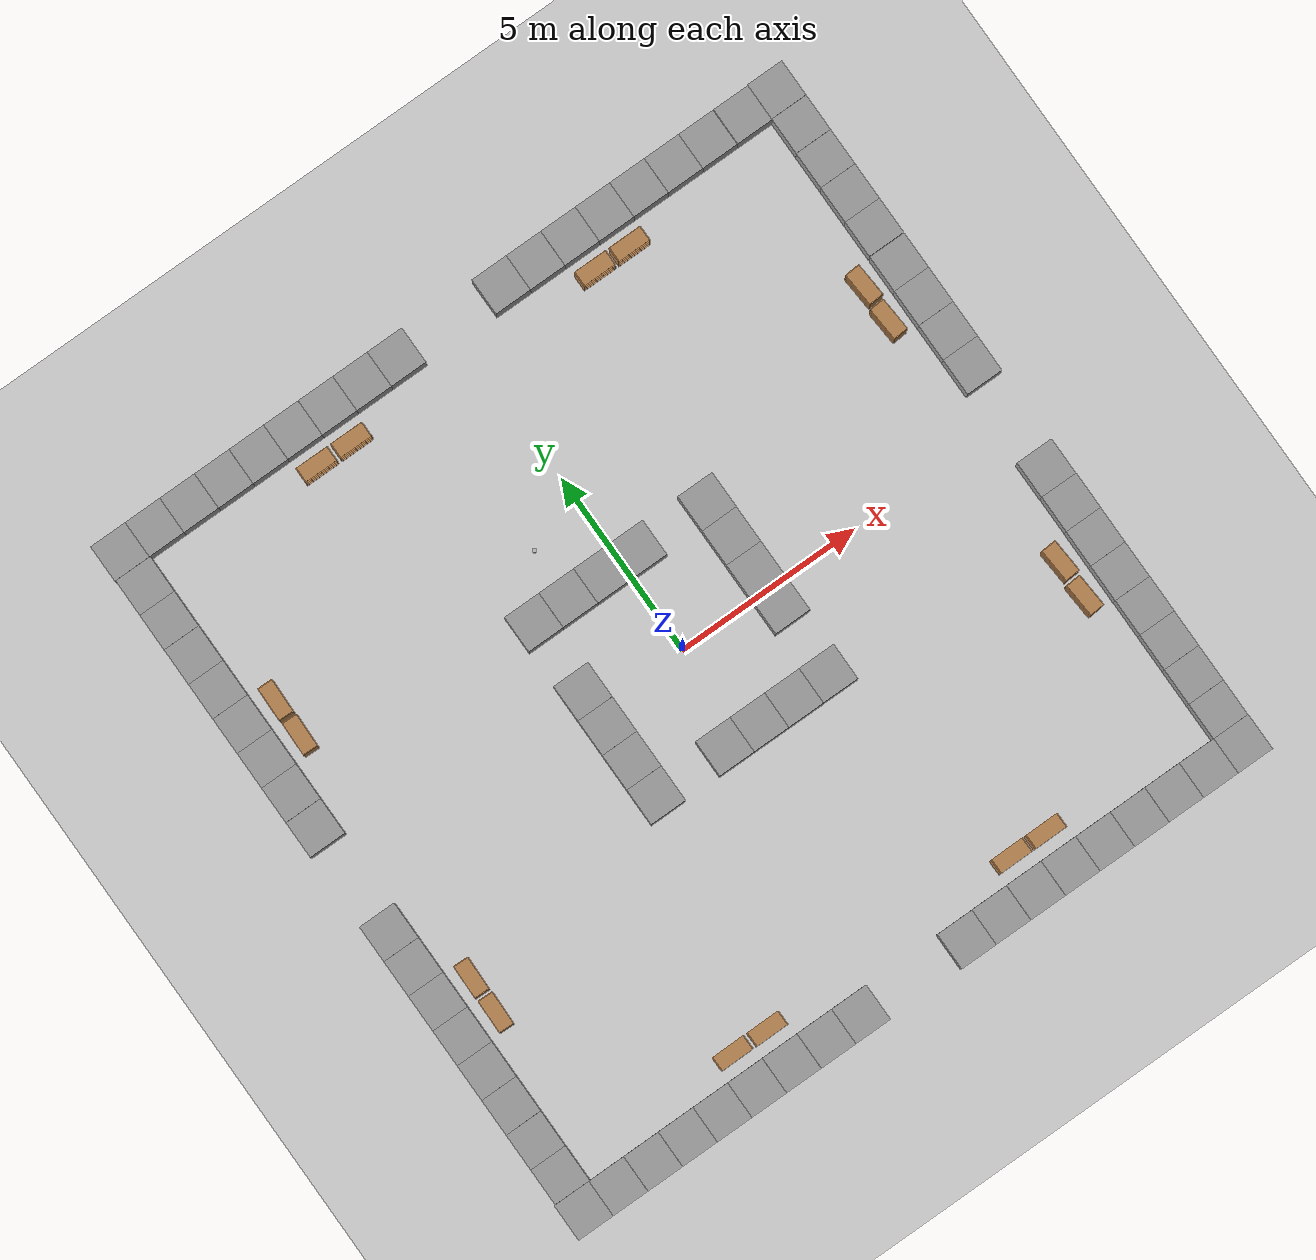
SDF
<sdf version="1.6">
 <world name="default">
  <light name="sun" type="directional">
   <pose>0 0 10 0 -0 0</pose>
   <diffuse>0.8 0.8 0.8 1</diffuse>
   <specular>0.2 0.2 0.2 1</specular>
   <attenuation>
    <range>1000</range>
    <constant>0.9</constant>
    <linear>0.01</linear>
    <quadratic>0.001</quadratic>
   </attenuation>
   <direction>-0.5 0.5 -1</direction>
  </light>
  <model name="ground_plane">
   <static>1</static>
   <link name="link">
    <collision name="collision">
     <geometry><plane><normal>0 0 1</normal><size>100 100</size></plane></geometry>
     <surface>
      <contact><collide_bitmask>65535</collide_bitmask></contact>
      <friction><ode><mu>100</mu><mu2>50</mu2></ode></friction>
     </surface>
    </collision>
    <visual name="visual">
     <cast_shadows>0</cast_shadows>
     <geometry><plane><normal>0 0 1</normal><size>100 100</size></plane></geometry>
     <material>
      <script><uri>file://media/materials/scripts/gazebo.material</uri><name>Gazebo/Grey</name></script>
     </material>
    </visual>
   </link>
  </model>
  <gravity>0 0 -9.8</gravity>
  <magnetic_field>6e-06 2.3e-05 -4.2e-05</magnetic_field>
  <atmosphere type="adiabatic"/>
  <physics name="default_physics" default="0" type="ode">
   <max_step_size>0.001</max_step_size>
   <real_time_factor>1</real_time_factor>
   <real_time_update_rate>1000</real_time_update_rate>
  </physics>
  <scene><ambient>0.4 0.4 0.4 1</ambient><background>0.7 0.7 0.7 1</background><shadows>1</shadows></scene>
  <spherical_coordinates>
   <surface_model>EARTH_WGS84</surface_model>
   <latitude_deg>0</latitude_deg>
   <longitude_deg>0</longitude_deg>
   <elevation>0</elevation>
   <heading_deg>0</heading_deg>
  </spherical_coordinates>
  <model name="unit_box_0">
   <pose>9.49071 -9.48407 0.499716 0.000569 -0 0.000249</pose>
   <link name="link">
    <inertial>
     <mass>1</mass>
     <inertia>
      <ixx>0.166667</ixx>
      <ixy>0</ixy>
      <ixz>0</ixz>
      <iyy>0.166667</iyy>
      <iyz>0</iyz>
      <izz>0.166667</izz>
     </inertia>
    </inertial>
    <collision name="collision"><geometry><box><size>1 1 1</size></box></geometry></collision>
    <visual name="visual">
     <geometry><box><size>1 1 1</size></box></geometry>
     <material>
      <script><name>Gazebo/Grey</name><uri>file://media/materials/scripts/gazebo.material</uri></script>
     </material>
    </visual>
   </link>
  </model>
  <model name="unit_box_1">
   <pose>9.47002 9.5409 0.49912 0 0 -1.3e-05</pose>
   <link name="link">
    <inertial>
     <mass>1</mass>
     <inertia>
      <ixx>0.166667</ixx>
      <ixy>0</ixy>
      <ixz>0</ixz>
      <iyy>0.166667</iyy>
      <iyz>0</iyz>
      <izz>0.166667</izz>
     </inertia>
    </inertial>
    <collision name="collision"><geometry><box><size>1 1 1</size></box></geometry></collision>
    <visual name="visual">
     <geometry><box><size>1 1 1</size></box></geometry>
     <material>
      <script><name>Gazebo/Grey</name><uri>file://media/materials/scripts/gazebo.material</uri></script>
     </material>
    </visual>
   </link>
  </model>
  <model name="unit_box_2">
   <pose>-9.56901 -9.47864 0.49912 0 -0 0.000136</pose>
   <link name="link">
    <inertial>
     <mass>1</mass>
     <inertia>
      <ixx>0.166667</ixx>
      <ixy>0</ixy>
      <ixz>0</ixz>
      <iyy>0.166667</iyy>
      <iyz>0</iyz>
      <izz>0.166667</izz>
     </inertia>
    </inertial>
    <collision name="collision"><geometry><box><size>1 1 1</size></box></geometry></collision>
    <visual name="visual">
     <geometry><box><size>1 1 1</size></box></geometry>
     <material>
      <script><name>Gazebo/Grey</name><uri>file://media/materials/scripts/gazebo.material</uri></script>
     </material>
    </visual>
   </link>
  </model>
  <model name="unit_box_3">
   <pose>-9.55233 9.54715 0.49907 -0.0001 -0 0.000678</pose>
   <link name="link">
    <inertial>
     <mass>1</mass>
     <inertia>
      <ixx>0.166667</ixx>
      <ixy>0</ixy>
      <ixz>0</ixz>
      <iyy>0.166667</iyy>
      <iyz>0</iyz>
      <izz>0.166667</izz>
     </inertia>
    </inertial>
    <collision name="collision"><geometry><box><size>1 1 1</size></box></geometry></collision>
    <visual name="visual">
     <geometry><box><size>1 1 1</size></box></geometry>
     <material>
      <script><name>Gazebo/Grey</name><uri>file://media/materials/scripts/gazebo.material</uri></script>
     </material>
    </visual>
   </link>
  </model>
  <model name="unit_box_4">
   <pose>9.48288 -8.48388 0.499798 0.000404 -1e-06 0.000265</pose>
   <link name="link">
    <inertial>
     <mass>1</mass>
     <inertia>
      <ixx>0.166667</ixx>
      <ixy>0</ixy>
      <ixz>0</ixz>
      <iyy>0.166667</iyy>
      <iyz>0</iyz>
      <izz>0.166667</izz>
     </inertia>
    </inertial>
    <collision name="collision"><geometry><box><size>1 1 1</size></box></geometry></collision>
    <visual name="visual">
     <geometry><box><size>1 1 1</size></box></geometry>
     <material>
      <script><name>Gazebo/Grey</name><uri>file://media/materials/scripts/gazebo.material</uri></script>
     </material>
    </visual>
   </link>
  </model>
  <model name="unit_box_5">
   <pose>9.48245 -7.48344 0.49907 -0 0.0001 0.000137</pose>
   <link name="link">
    <inertial>
     <mass>1</mass>
     <inertia>
      <ixx>0.166667</ixx>
      <ixy>0</ixy>
      <ixz>0</ixz>
      <iyy>0.166667</iyy>
      <iyz>0</iyz>
      <izz>0.166667</izz>
     </inertia>
    </inertial>
    <collision name="collision"><geometry><box><size>1 1 1</size></box></geometry></collision>
    <visual name="visual">
     <geometry><box><size>1 1 1</size></box></geometry>
     <material>
      <script><name>Gazebo/Grey</name><uri>file://media/materials/scripts/gazebo.material</uri></script>
     </material>
    </visual>
   </link>
  </model>
  <model name="unit_box_6">
   <pose>9.48373 -6.48254 0.49907 0 -0.0001 0.000235</pose>
   <link name="link">
    <inertial>
     <mass>1</mass>
     <inertia>
      <ixx>0.166667</ixx>
      <ixy>0</ixy>
      <ixz>0</ixz>
      <iyy>0.166667</iyy>
      <iyz>0</iyz>
      <izz>0.166667</izz>
     </inertia>
    </inertial>
    <collision name="collision"><geometry><box><size>1 1 1</size></box></geometry></collision>
    <visual name="visual">
     <geometry><box><size>1 1 1</size></box></geometry>
     <material>
      <script><name>Gazebo/Grey</name><uri>file://media/materials/scripts/gazebo.material</uri></script>
     </material>
    </visual>
   </link>
  </model>
  <model name="unit_box_7">
   <pose>9.48675 -5.48245 0.5 0 -0 0.000238</pose>
   <link name="link">
    <inertial>
     <mass>1</mass>
     <inertia>
      <ixx>0.166667</ixx>
      <ixy>0</ixy>
      <ixz>0</ixz>
      <iyy>0.166667</iyy>
      <iyz>0</iyz>
      <izz>0.166667</izz>
     </inertia>
    </inertial>
    <collision name="collision"><geometry><box><size>1 1 1</size></box></geometry></collision>
    <visual name="visual">
     <geometry><box><size>1 1 1</size></box></geometry>
     <material>
      <script><name>Gazebo/Grey</name><uri>file://media/materials/scripts/gazebo.material</uri></script>
     </material>
    </visual>
   </link>
  </model>
  <model name="unit_box_8">
   <pose>9.48325 -4.48211 0.49515 0 0.0001 0.000184</pose>
   <link name="link">
    <inertial>
     <mass>1</mass>
     <inertia>
      <ixx>0.166667</ixx>
      <ixy>0</ixy>
      <ixz>0</ixz>
      <iyy>0.166667</iyy>
      <iyz>0</iyz>
      <izz>0.166667</izz>
     </inertia>
    </inertial>
    <collision name="collision"><geometry><box><size>1 1 1</size></box></geometry></collision>
    <visual name="visual">
     <geometry><box><size>1 1 1</size></box></geometry>
     <material>
      <script><name>Gazebo/Grey</name><uri>file://media/materials/scripts/gazebo.material</uri></script>
     </material>
    </visual>
   </link>
  </model>
  <model name="unit_box_9">
   <pose>9.48361 -3.48174 0.49907 -0.0001 -0 -6.1e-05</pose>
   <link name="link">
    <inertial>
     <mass>1</mass>
     <inertia>
      <ixx>0.166667</ixx>
      <ixy>0</ixy>
      <ixz>0</ixz>
      <iyy>0.166667</iyy>
      <iyz>0</iyz>
      <izz>0.166667</izz>
     </inertia>
    </inertial>
    <collision name="collision"><geometry><box><size>1 1 1</size></box></geometry></collision>
    <visual name="visual">
     <geometry><box><size>1 1 1</size></box></geometry>
     <material>
      <script><name>Gazebo/Grey</name><uri>file://media/materials/scripts/gazebo.material</uri></script>
     </material>
    </visual>
   </link>
  </model>
  <model name="unit_box_10">
   <pose>9.4879 -2.48152 0.49902 0 0 -0.000306</pose>
   <link name="link">
    <inertial>
     <mass>1</mass>
     <inertia>
      <ixx>0.166667</ixx>
      <ixy>0</ixy>
      <ixz>0</ixz>
      <iyy>0.166667</iyy>
      <iyz>0</iyz>
      <izz>0.166667</izz>
     </inertia>
    </inertial>
    <collision name="collision"><geometry><box><size>1 1 1</size></box></geometry></collision>
    <visual name="visual">
     <geometry><box><size>1 1 1</size></box></geometry>
     <material>
      <script><name>Gazebo/Grey</name><uri>file://media/materials/scripts/gazebo.material</uri></script>
     </material>
    </visual>
   </link>
  </model>
  <model name="unit_box_11">
   <pose>9.48117 -1.48142 0.49967 0 -0.00066 -0.000141</pose>
   <link name="link">
    <inertial>
     <mass>1</mass>
     <inertia>
      <ixx>0.166667</ixx>
      <ixy>0</ixy>
      <ixz>0</ixz>
      <iyy>0.166667</iyy>
      <iyz>0</iyz>
      <izz>0.166667</izz>
     </inertia>
    </inertial>
    <collision name="collision"><geometry><box><size>1 1 1</size></box></geometry></collision>
    <visual name="visual">
     <geometry><box><size>1 1 1</size></box></geometry>
     <material>
      <script><name>Gazebo/Grey</name><uri>file://media/materials/scripts/gazebo.material</uri></script>
     </material>
    </visual>
   </link>
  </model>
  <model name="unit_box_12">
   <pose>9.46932 8.53598 0.49912 0 0 -0.000725</pose>
   <link name="link">
    <inertial>
     <mass>1</mass>
     <inertia>
      <ixx>0.166667</ixx>
      <ixy>0</ixy>
      <ixz>0</ixz>
      <iyy>0.166667</iyy>
      <iyz>0</iyz>
      <izz>0.166667</izz>
     </inertia>
    </inertial>
    <collision name="collision"><geometry><box><size>1 1 1</size></box></geometry></collision>
    <visual name="visual">
     <geometry><box><size>1 1 1</size></box></geometry>
     <material>
      <script><name>Gazebo/Grey</name><uri>file://media/materials/scripts/gazebo.material</uri></script>
     </material>
    </visual>
   </link>
  </model>
  <model name="unit_box_13">
   <pose>9.46832 7.53189 0.499683 -0.000633 0 0.0004</pose>
   <link name="link">
    <inertial>
     <mass>1</mass>
     <inertia>
      <ixx>0.166667</ixx>
      <ixy>0</ixy>
      <ixz>0</ixz>
      <iyy>0.166667</iyy>
      <iyz>0</iyz>
      <izz>0.166667</izz>
     </inertia>
    </inertial>
    <collision name="collision"><geometry><box><size>1 1 1</size></box></geometry></collision>
    <visual name="visual">
     <geometry><box><size>1 1 1</size></box></geometry>
     <material>
      <script><name>Gazebo/Grey</name><uri>file://media/materials/scripts/gazebo.material</uri></script>
     </material>
    </visual>
   </link>
  </model>
  <model name="unit_box_14">
   <pose>9.46841 6.53108 0.49907 -0 -0.0001 0.000148</pose>
   <link name="link">
    <inertial>
     <mass>1</mass>
     <inertia>
      <ixx>0.166667</ixx>
      <ixy>0</ixy>
      <ixz>0</ixz>
      <iyy>0.166667</iyy>
      <iyz>0</iyz>
      <izz>0.166667</izz>
     </inertia>
    </inertial>
    <collision name="collision"><geometry><box><size>1 1 1</size></box></geometry></collision>
    <visual name="visual">
     <geometry><box><size>1 1 1</size></box></geometry>
     <material>
      <script><name>Gazebo/Grey</name><uri>file://media/materials/scripts/gazebo.material</uri></script>
     </material>
    </visual>
   </link>
  </model>
  <model name="unit_box_15">
   <pose>9.46864 5.53104 0.49912 0 -0 0.000156</pose>
   <link name="link">
    <inertial>
     <mass>1</mass>
     <inertia>
      <ixx>0.166667</ixx>
      <ixy>0</ixy>
      <ixz>0</ixz>
      <iyy>0.166667</iyy>
      <iyz>0</iyz>
      <izz>0.166667</izz>
     </inertia>
    </inertial>
    <collision name="collision"><geometry><box><size>1 1 1</size></box></geometry></collision>
    <visual name="visual">
     <geometry><box><size>1 1 1</size></box></geometry>
     <material>
      <script><name>Gazebo/Grey</name><uri>file://media/materials/scripts/gazebo.material</uri></script>
     </material>
    </visual>
   </link>
  </model>
  <model name="unit_box_16">
   <pose>9.46813 4.51827 0.49912 0 0 -9.1e-05</pose>
   <link name="link">
    <inertial>
     <mass>1</mass>
     <inertia>
      <ixx>0.166667</ixx>
      <ixy>0</ixy>
      <ixz>0</ixz>
      <iyy>0.166667</iyy>
      <iyz>0</iyz>
      <izz>0.166667</izz>
     </inertia>
    </inertial>
    <collision name="collision"><geometry><box><size>1 1 1</size></box></geometry></collision>
    <visual name="visual">
     <geometry><box><size>1 1 1</size></box></geometry>
     <material>
      <script><name>Gazebo/Grey</name><uri>file://media/materials/scripts/gazebo.material</uri></script>
     </material>
    </visual>
   </link>
  </model>
  <model name="unit_box_17">
   <pose>9.46838 3.51825 0.49912 0 0 -9.3e-05</pose>
   <link name="link">
    <inertial>
     <mass>1</mass>
     <inertia>
      <ixx>0.166667</ixx>
      <ixy>0</ixy>
      <ixz>0</ixz>
      <iyy>0.166667</iyy>
      <iyz>0</iyz>
      <izz>0.166667</izz>
     </inertia>
    </inertial>
    <collision name="collision"><geometry><box><size>1 1 1</size></box></geometry></collision>
    <visual name="visual">
     <geometry><box><size>1 1 1</size></box></geometry>
     <material>
      <script><name>Gazebo/Grey</name><uri>file://media/materials/scripts/gazebo.material</uri></script>
     </material>
    </visual>
   </link>
  </model>
  <model name="unit_box_18">
   <pose>9.46805 2.51724 0.49912 0 -0 0.000151</pose>
   <link name="link">
    <inertial>
     <mass>1</mass>
     <inertia>
      <ixx>0.166667</ixx>
      <ixy>0</ixy>
      <ixz>0</ixz>
      <iyy>0.166667</iyy>
      <iyz>0</iyz>
      <izz>0.166667</izz>
     </inertia>
    </inertial>
    <collision name="collision"><geometry><box><size>1 1 1</size></box></geometry></collision>
    <visual name="visual">
     <geometry><box><size>1 1 1</size></box></geometry>
     <material>
      <script><name>Gazebo/Grey</name><uri>file://media/materials/scripts/gazebo.material</uri></script>
     </material>
    </visual>
   </link>
  </model>
  <model name="unit_box_19">
   <pose>9.46806 1.51722 0.49912 0 -0 0.000141</pose>
   <link name="link">
    <inertial>
     <mass>1</mass>
     <inertia>
      <ixx>0.166667</ixx>
      <ixy>0</ixy>
      <ixz>0</ixz>
      <iyy>0.166667</iyy>
      <iyz>0</iyz>
      <izz>0.166667</izz>
     </inertia>
    </inertial>
    <collision name="collision"><geometry><box><size>1 1 1</size></box></geometry></collision>
    <visual name="visual">
     <geometry><box><size>1 1 1</size></box></geometry>
     <material>
      <script><name>Gazebo/Grey</name><uri>file://media/materials/scripts/gazebo.material</uri></script>
     </material>
    </visual>
   </link>
  </model>
  <model name="unit_box_20">
   <pose>8.49061 -9.48537 0.499802 -0.000397 -0 0.000264</pose>
   <link name="link">
    <inertial>
     <mass>1</mass>
     <inertia>
      <ixx>0.166667</ixx>
      <ixy>0</ixy>
      <ixz>0</ixz>
      <iyy>0.166667</iyy>
      <iyz>0</iyz>
      <izz>0.166667</izz>
     </inertia>
    </inertial>
    <collision name="collision"><geometry><box><size>1 1 1</size></box></geometry></collision>
    <visual name="visual">
     <geometry><box><size>1 1 1</size></box></geometry>
     <material>
      <script><name>Gazebo/Grey</name><uri>file://media/materials/scripts/gazebo.material</uri></script>
     </material>
    </visual>
   </link>
  </model>
  <model name="unit_box_21">
   <pose>7.49051 -9.48392 0.49912 0 -0 0.000436</pose>
   <link name="link">
    <inertial>
     <mass>1</mass>
     <inertia>
      <ixx>0.166667</ixx>
      <ixy>0</ixy>
      <ixz>0</ixz>
      <iyy>0.166667</iyy>
      <iyz>0</iyz>
      <izz>0.166667</izz>
     </inertia>
    </inertial>
    <collision name="collision"><geometry><box><size>1 1 1</size></box></geometry></collision>
    <visual name="visual">
     <geometry><box><size>1 1 1</size></box></geometry>
     <material>
      <script><name>Gazebo/Grey</name><uri>file://media/materials/scripts/gazebo.material</uri></script>
     </material>
    </visual>
   </link>
  </model>
  <model name="unit_box_22">
   <pose>6.49017 -9.48723 0.49912 0 -0 0.000433</pose>
   <link name="link">
    <inertial>
     <mass>1</mass>
     <inertia>
      <ixx>0.166667</ixx>
      <ixy>0</ixy>
      <ixz>0</ixz>
      <iyy>0.166667</iyy>
      <iyz>0</iyz>
      <izz>0.166667</izz>
     </inertia>
    </inertial>
    <collision name="collision"><geometry><box><size>1 1 1</size></box></geometry></collision>
    <visual name="visual">
     <geometry><box><size>1 1 1</size></box></geometry>
     <material>
      <script><name>Gazebo/Grey</name><uri>file://media/materials/scripts/gazebo.material</uri></script>
     </material>
    </visual>
   </link>
  </model>
  <model name="unit_box_23">
   <pose>5.4901 -9.48407 0.49912 0 -0 0.000433</pose>
   <link name="link">
    <inertial>
     <mass>1</mass>
     <inertia>
      <ixx>0.166667</ixx>
      <ixy>0</ixy>
      <ixz>0</ixz>
      <iyy>0.166667</iyy>
      <iyz>0</iyz>
      <izz>0.166667</izz>
     </inertia>
    </inertial>
    <collision name="collision"><geometry><box><size>1 1 1</size></box></geometry></collision>
    <visual name="visual">
     <geometry><box><size>1 1 1</size></box></geometry>
     <material>
      <script><name>Gazebo/Grey</name><uri>file://media/materials/scripts/gazebo.material</uri></script>
     </material>
    </visual>
   </link>
  </model>
  <model name="unit_box_24">
   <pose>4.48984 -9.48419 0.49912 0 -0 0.00046</pose>
   <link name="link">
    <inertial>
     <mass>1</mass>
     <inertia>
      <ixx>0.166667</ixx>
      <ixy>0</ixy>
      <ixz>0</ixz>
      <iyy>0.166667</iyy>
      <iyz>0</iyz>
      <izz>0.166667</izz>
     </inertia>
    </inertial>
    <collision name="collision"><geometry><box><size>1 1 1</size></box></geometry></collision>
    <visual name="visual">
     <geometry><box><size>1 1 1</size></box></geometry>
     <material>
      <script><name>Gazebo/Grey</name><uri>file://media/materials/scripts/gazebo.material</uri></script>
     </material>
    </visual>
   </link>
  </model>
  <model name="unit_box_25">
   <pose>3.48859 -9.48345 0.49912 0 0 -0.00034</pose>
   <link name="link">
    <inertial>
     <mass>1</mass>
     <inertia>
      <ixx>0.166667</ixx>
      <ixy>0</ixy>
      <ixz>0</ixz>
      <iyy>0.166667</iyy>
      <iyz>0</iyz>
      <izz>0.166667</izz>
     </inertia>
    </inertial>
    <collision name="collision"><geometry><box><size>1 1 1</size></box></geometry></collision>
    <visual name="visual">
     <geometry><box><size>1 1 1</size></box></geometry>
     <material>
      <script><name>Gazebo/Grey</name><uri>file://media/materials/scripts/gazebo.material</uri></script>
     </material>
    </visual>
   </link>
  </model>
  <model name="unit_box_26">
   <pose>2.4868 -9.48212 0.49912 0 0 -0.001681</pose>
   <link name="link">
    <inertial>
     <mass>1</mass>
     <inertia>
      <ixx>0.166667</ixx>
      <ixy>0</ixy>
      <ixz>0</ixz>
      <iyy>0.166667</iyy>
      <iyz>0</iyz>
      <izz>0.166667</izz>
     </inertia>
    </inertial>
    <collision name="collision"><geometry><box><size>1 1 1</size></box></geometry></collision>
    <visual name="visual">
     <geometry><box><size>1 1 1</size></box></geometry>
     <material>
      <script><name>Gazebo/Grey</name><uri>file://media/materials/scripts/gazebo.material</uri></script>
     </material>
    </visual>
   </link>
  </model>
  <model name="unit_box_27">
   <pose>1.48669 -9.4846 0.49912 0 0 -0.001478</pose>
   <link name="link">
    <inertial>
     <mass>1</mass>
     <inertia>
      <ixx>0.166667</ixx>
      <ixy>0</ixy>
      <ixz>0</ixz>
      <iyy>0.166667</iyy>
      <iyz>0</iyz>
      <izz>0.166667</izz>
     </inertia>
    </inertial>
    <collision name="collision"><geometry><box><size>1 1 1</size></box></geometry></collision>
    <visual name="visual">
     <geometry><box><size>1 1 1</size></box></geometry>
     <material>
      <script><name>Gazebo/Grey</name><uri>file://media/materials/scripts/gazebo.material</uri></script>
     </material>
    </visual>
   </link>
  </model>
  <model name="unit_box_28">
   <pose>-8.5686 -9.47836 0.49912 0 -0 0.00016</pose>
   <link name="link">
    <inertial>
     <mass>1</mass>
     <inertia>
      <ixx>0.166667</ixx>
      <ixy>0</ixy>
      <ixz>0</ixz>
      <iyy>0.166667</iyy>
      <iyz>0</iyz>
      <izz>0.166667</izz>
     </inertia>
    </inertial>
    <collision name="collision"><geometry><box><size>1 1 1</size></box></geometry></collision>
    <visual name="visual">
     <geometry><box><size>1 1 1</size></box></geometry>
     <material>
      <script><name>Gazebo/Grey</name><uri>file://media/materials/scripts/gazebo.material</uri></script>
     </material>
    </visual>
   </link>
  </model>
  <model name="unit_box_29">
   <pose>-7.56783 -9.4789 0.499798 0.000404 1e-06 -2.2e-05</pose>
   <link name="link">
    <inertial>
     <mass>1</mass>
     <inertia>
      <ixx>0.166667</ixx>
      <ixy>0</ixy>
      <ixz>0</ixz>
      <iyy>0.166667</iyy>
      <iyz>0</iyz>
      <izz>0.166667</izz>
     </inertia>
    </inertial>
    <collision name="collision"><geometry><box><size>1 1 1</size></box></geometry></collision>
    <visual name="visual">
     <geometry><box><size>1 1 1</size></box></geometry>
     <material>
      <script><name>Gazebo/Grey</name><uri>file://media/materials/scripts/gazebo.material</uri></script>
     </material>
    </visual>
   </link>
  </model>
  <model name="unit_box_30">
   <pose>-6.56772 -9.47776 0.49912 0 0 -1.9e-05</pose>
   <link name="link">
    <inertial>
     <mass>1</mass>
     <inertia>
      <ixx>0.166667</ixx>
      <ixy>0</ixy>
      <ixz>0</ixz>
      <iyy>0.166667</iyy>
      <iyz>0</iyz>
      <izz>0.166667</izz>
     </inertia>
    </inertial>
    <collision name="collision"><geometry><box><size>1 1 1</size></box></geometry></collision>
    <visual name="visual">
     <geometry><box><size>1 1 1</size></box></geometry>
     <material>
      <script><name>Gazebo/Grey</name><uri>file://media/materials/scripts/gazebo.material</uri></script>
     </material>
    </visual>
   </link>
  </model>
  <model name="unit_box_31">
   <pose>-5.5675 -9.47915 0.49912 0 0 -0.000171</pose>
   <link name="link">
    <inertial>
     <mass>1</mass>
     <inertia>
      <ixx>0.166667</ixx>
      <ixy>0</ixy>
      <ixz>0</ixz>
      <iyy>0.166667</iyy>
      <iyz>0</iyz>
      <izz>0.166667</izz>
     </inertia>
    </inertial>
    <collision name="collision"><geometry><box><size>1 1 1</size></box></geometry></collision>
    <visual name="visual">
     <geometry><box><size>1 1 1</size></box></geometry>
     <material>
      <script><name>Gazebo/Grey</name><uri>file://media/materials/scripts/gazebo.material</uri></script>
     </material>
    </visual>
   </link>
  </model>
  <model name="unit_box_32">
   <pose>-4.56729 -9.47952 0.49912 0 0 -0.000396</pose>
   <link name="link">
    <inertial>
     <mass>1</mass>
     <inertia>
      <ixx>0.166667</ixx>
      <ixy>0</ixy>
      <ixz>0</ixz>
      <iyy>0.166667</iyy>
      <iyz>0</iyz>
      <izz>0.166667</izz>
     </inertia>
    </inertial>
    <collision name="collision"><geometry><box><size>1 1 1</size></box></geometry></collision>
    <visual name="visual">
     <geometry><box><size>1 1 1</size></box></geometry>
     <material>
      <script><name>Gazebo/Grey</name><uri>file://media/materials/scripts/gazebo.material</uri></script>
     </material>
    </visual>
   </link>
  </model>
  <model name="unit_box_33">
   <pose>-3.56687 -9.47813 0.49912 0 0 -0.000941</pose>
   <link name="link">
    <inertial>
     <mass>1</mass>
     <inertia>
      <ixx>0.166667</ixx>
      <ixy>0</ixy>
      <ixz>0</ixz>
      <iyy>0.166667</iyy>
      <iyz>0</iyz>
      <izz>0.166667</izz>
     </inertia>
    </inertial>
    <collision name="collision"><geometry><box><size>1 1 1</size></box></geometry></collision>
    <visual name="visual">
     <geometry><box><size>1 1 1</size></box></geometry>
     <material>
      <script><name>Gazebo/Grey</name><uri>file://media/materials/scripts/gazebo.material</uri></script>
     </material>
    </visual>
   </link>
  </model>
  <model name="unit_box_34">
   <pose>-2.56595 -9.47892 0.49912 0 -0 0.000402</pose>
   <link name="link">
    <inertial>
     <mass>1</mass>
     <inertia>
      <ixx>0.166667</ixx>
      <ixy>0</ixy>
      <ixz>0</ixz>
      <iyy>0.166667</iyy>
      <iyz>0</iyz>
      <izz>0.166667</izz>
     </inertia>
    </inertial>
    <collision name="collision"><geometry><box><size>1 1 1</size></box></geometry></collision>
    <visual name="visual">
     <geometry><box><size>1 1 1</size></box></geometry>
     <material>
      <script><name>Gazebo/Grey</name><uri>file://media/materials/scripts/gazebo.material</uri></script>
     </material>
    </visual>
   </link>
  </model>
  <model name="unit_box_35">
   <pose>-1.56588 -9.47913 0.49912 0 -0 0.000371</pose>
   <link name="link">
    <inertial>
     <mass>1</mass>
     <inertia>
      <ixx>0.166667</ixx>
      <ixy>0</ixy>
      <ixz>0</ixz>
      <iyy>0.166667</iyy>
      <iyz>0</iyz>
      <izz>0.166667</izz>
     </inertia>
    </inertial>
    <collision name="collision"><geometry><box><size>1 1 1</size></box></geometry></collision>
    <visual name="visual">
     <geometry><box><size>1 1 1</size></box></geometry>
     <material>
      <script><name>Gazebo/Grey</name><uri>file://media/materials/scripts/gazebo.material</uri></script>
     </material>
    </visual>
   </link>
  </model>
  <model name="unit_box_36_0">
   <pose>-9.53197 8.54457 0.498653 0 0.000735 -0.003757</pose>
   <link name="link">
    <inertial>
     <mass>1</mass>
     <inertia>
      <ixx>0.166667</ixx>
      <ixy>0</ixy>
      <ixz>0</ixz>
      <iyy>0.166667</iyy>
      <iyz>0</iyz>
      <izz>0.166667</izz>
     </inertia>
    </inertial>
    <collision name="collision"><geometry><box><size>1 1 1</size></box></geometry></collision>
    <visual name="visual">
     <geometry><box><size>1 1 1</size></box></geometry>
     <material>
      <script><name>Gazebo/Grey</name><uri>file://media/materials/scripts/gazebo.material</uri></script>
     </material>
    </visual>
   </link>
  </model>
  <model name="unit_box_36_1">
   <pose>-9.5358 7.54446 0.49912 0 0 -0.003704</pose>
   <link name="link">
    <inertial>
     <mass>1</mass>
     <inertia>
      <ixx>0.166667</ixx>
      <ixy>0</ixy>
      <ixz>0</ixz>
      <iyy>0.166667</iyy>
      <iyz>0</iyz>
      <izz>0.166667</izz>
     </inertia>
    </inertial>
    <collision name="collision"><geometry><box><size>1 1 1</size></box></geometry></collision>
    <visual name="visual">
     <geometry><box><size>1 1 1</size></box></geometry>
     <material>
      <script><name>Gazebo/Grey</name><uri>file://media/materials/scripts/gazebo.material</uri></script>
     </material>
    </visual>
   </link>
  </model>
  <model name="unit_box_36_2">
   <pose>-9.53522 6.54264 0.49907 0 -0.0001 -0.001229</pose>
   <link name="link">
    <inertial>
     <mass>1</mass>
     <inertia>
      <ixx>0.166667</ixx>
      <ixy>0</ixy>
      <ixz>0</ixz>
      <iyy>0.166667</iyy>
      <iyz>0</iyz>
      <izz>0.166667</izz>
     </inertia>
    </inertial>
    <collision name="collision"><geometry><box><size>1 1 1</size></box></geometry></collision>
    <visual name="visual">
     <geometry><box><size>1 1 1</size></box></geometry>
     <material>
      <script><name>Gazebo/Grey</name><uri>file://media/materials/scripts/gazebo.material</uri></script>
     </material>
    </visual>
   </link>
  </model>
  <model name="unit_box_36_3">
   <pose>-9.53613 5.54258 0.5 0 0 -0.001269</pose>
   <link name="link">
    <inertial>
     <mass>1</mass>
     <inertia>
      <ixx>0.166667</ixx>
      <ixy>0</ixy>
      <ixz>0</ixz>
      <iyy>0.166667</iyy>
      <iyz>0</iyz>
      <izz>0.166667</izz>
     </inertia>
    </inertial>
    <collision name="collision"><geometry><box><size>1 1 1</size></box></geometry></collision>
    <visual name="visual">
     <geometry><box><size>1 1 1</size></box></geometry>
     <material>
      <script><name>Gazebo/Grey</name><uri>file://media/materials/scripts/gazebo.material</uri></script>
     </material>
    </visual>
   </link>
  </model>
  <model name="unit_box_36_4">
   <pose>-9.5363 4.54199 0.49912 0 0 -0.000289</pose>
   <link name="link">
    <inertial>
     <mass>1</mass>
     <inertia>
      <ixx>0.166667</ixx>
      <ixy>0</ixy>
      <ixz>0</ixz>
      <iyy>0.166667</iyy>
      <iyz>0</iyz>
      <izz>0.166667</izz>
     </inertia>
    </inertial>
    <collision name="collision"><geometry><box><size>1 1 1</size></box></geometry></collision>
    <visual name="visual">
     <geometry><box><size>1 1 1</size></box></geometry>
     <material>
      <script><name>Gazebo/Grey</name><uri>file://media/materials/scripts/gazebo.material</uri></script>
     </material>
    </visual>
   </link>
  </model>
  <model name="unit_box_36_5">
   <pose>-9.53596 3.54171 0.49907 0 0.0001 -0.000659</pose>
   <link name="link">
    <inertial>
     <mass>1</mass>
     <inertia>
      <ixx>0.166667</ixx>
      <ixy>0</ixy>
      <ixz>0</ixz>
      <iyy>0.166667</iyy>
      <iyz>0</iyz>
      <izz>0.166667</izz>
     </inertia>
    </inertial>
    <collision name="collision"><geometry><box><size>1 1 1</size></box></geometry></collision>
    <visual name="visual">
     <geometry><box><size>1 1 1</size></box></geometry>
     <material>
      <script><name>Gazebo/Grey</name><uri>file://media/materials/scripts/gazebo.material</uri></script>
     </material>
    </visual>
   </link>
  </model>
  <model name="unit_box_36_6">
   <pose>-9.53743 2.54152 0.49912 0 0 -0.000437</pose>
   <link name="link">
    <inertial>
     <mass>1</mass>
     <inertia>
      <ixx>0.166667</ixx>
      <ixy>0</ixy>
      <ixz>0</ixz>
      <iyy>0.166667</iyy>
      <iyz>0</iyz>
      <izz>0.166667</izz>
     </inertia>
    </inertial>
    <collision name="collision"><geometry><box><size>1 1 1</size></box></geometry></collision>
    <visual name="visual">
     <geometry><box><size>1 1 1</size></box></geometry>
     <material>
      <script><name>Gazebo/Grey</name><uri>file://media/materials/scripts/gazebo.material</uri></script>
     </material>
    </visual>
   </link>
  </model>
  <model name="unit_box_36_7">
   <pose>-9.53709 1.53746 0.49912 0 0 -5e-06</pose>
   <link name="link">
    <inertial>
     <mass>1</mass>
     <inertia>
      <ixx>0.166667</ixx>
      <ixy>0</ixy>
      <ixz>0</ixz>
      <iyy>0.166667</iyy>
      <iyz>0</iyz>
      <izz>0.166667</izz>
     </inertia>
    </inertial>
    <collision name="collision"><geometry><box><size>1 1 1</size></box></geometry></collision>
    <visual name="visual">
     <geometry><box><size>1 1 1</size></box></geometry>
     <material>
      <script><name>Gazebo/Grey</name><uri>file://media/materials/scripts/gazebo.material</uri></script>
     </material>
    </visual>
   </link>
  </model>
  <model name="unit_box_36_8">
   <pose>-9.53766 -1.47324 0.49912 0 0 -0.000428</pose>
   <link name="link">
    <inertial>
     <mass>1</mass>
     <inertia>
      <ixx>0.166667</ixx>
      <ixy>0</ixy>
      <ixz>0</ixz>
      <iyy>0.166667</iyy>
      <iyz>0</iyz>
      <izz>0.166667</izz>
     </inertia>
    </inertial>
    <collision name="collision"><geometry><box><size>1 1 1</size></box></geometry></collision>
    <visual name="visual">
     <geometry><box><size>1 1 1</size></box></geometry>
     <material>
      <script><name>Gazebo/Grey</name><uri>file://media/materials/scripts/gazebo.material</uri></script>
     </material>
    </visual>
   </link>
  </model>
  <model name="unit_box_36_9">
   <pose>-9.53797 -2.47367 0.49912 0 0 -9e-05</pose>
   <link name="link">
    <inertial>
     <mass>1</mass>
     <inertia>
      <ixx>0.166667</ixx>
      <ixy>0</ixy>
      <ixz>0</ixz>
      <iyy>0.166667</iyy>
      <iyz>0</iyz>
      <izz>0.166667</izz>
     </inertia>
    </inertial>
    <collision name="collision"><geometry><box><size>1 1 1</size></box></geometry></collision>
    <visual name="visual">
     <geometry><box><size>1 1 1</size></box></geometry>
     <material>
      <script><name>Gazebo/Grey</name><uri>file://media/materials/scripts/gazebo.material</uri></script>
     </material>
    </visual>
   </link>
  </model>
  <model name="unit_box_36_10">
   <pose>-9.53735 -3.47375 0.49912 0 0 -4.5e-05</pose>
   <link name="link">
    <inertial>
     <mass>1</mass>
     <inertia>
      <ixx>0.166667</ixx>
      <ixy>0</ixy>
      <ixz>0</ixz>
      <iyy>0.166667</iyy>
      <iyz>0</iyz>
      <izz>0.166667</izz>
     </inertia>
    </inertial>
    <collision name="collision"><geometry><box><size>1 1 1</size></box></geometry></collision>
    <visual name="visual">
     <geometry><box><size>1 1 1</size></box></geometry>
     <material>
      <script><name>Gazebo/Grey</name><uri>file://media/materials/scripts/gazebo.material</uri></script>
     </material>
    </visual>
   </link>
  </model>
  <model name="unit_box_36_11">
   <pose>-9.53788 -4.4738 0.49912 0 0 -3.2e-05</pose>
   <link name="link">
    <inertial>
     <mass>1</mass>
     <inertia>
      <ixx>0.166667</ixx>
      <ixy>0</ixy>
      <ixz>0</ixz>
      <iyy>0.166667</iyy>
      <iyz>0</iyz>
      <izz>0.166667</izz>
     </inertia>
    </inertial>
    <collision name="collision"><geometry><box><size>1 1 1</size></box></geometry></collision>
    <visual name="visual">
     <geometry><box><size>1 1 1</size></box></geometry>
     <material>
      <script><name>Gazebo/Grey</name><uri>file://media/materials/scripts/gazebo.material</uri></script>
     </material>
    </visual>
   </link>
  </model>
  <model name="unit_box_36_12">
   <pose>-9.53806 -5.47391 0.49912 0 0 -3.6e-05</pose>
   <link name="link">
    <inertial>
     <mass>1</mass>
     <inertia>
      <ixx>0.166667</ixx>
      <ixy>0</ixy>
      <ixz>0</ixz>
      <iyy>0.166667</iyy>
      <iyz>0</iyz>
      <izz>0.166667</izz>
     </inertia>
    </inertial>
    <collision name="collision"><geometry><box><size>1 1 1</size></box></geometry></collision>
    <visual name="visual">
     <geometry><box><size>1 1 1</size></box></geometry>
     <material>
      <script><name>Gazebo/Grey</name><uri>file://media/materials/scripts/gazebo.material</uri></script>
     </material>
    </visual>
   </link>
  </model>
  <model name="unit_box_36_13">
   <pose>-9.5375 -6.47436 0.49907 0.0001 -0 0.00037</pose>
   <link name="link">
    <inertial>
     <mass>1</mass>
     <inertia>
      <ixx>0.166667</ixx>
      <ixy>0</ixy>
      <ixz>0</ixz>
      <iyy>0.166667</iyy>
      <iyz>0</iyz>
      <izz>0.166667</izz>
     </inertia>
    </inertial>
    <collision name="collision"><geometry><box><size>1 1 1</size></box></geometry></collision>
    <visual name="visual">
     <geometry><box><size>1 1 1</size></box></geometry>
     <material>
      <script><name>Gazebo/Grey</name><uri>file://media/materials/scripts/gazebo.material</uri></script>
     </material>
    </visual>
   </link>
  </model>
  <model name="unit_box_36_14">
   <pose>-9.53835 -7.47657 0.499798 -0.000404 0 -0.00123</pose>
   <link name="link">
    <inertial>
     <mass>1</mass>
     <inertia>
      <ixx>0.166667</ixx>
      <ixy>0</ixy>
      <ixz>0</ixz>
      <iyy>0.166667</iyy>
      <iyz>0</iyz>
      <izz>0.166667</izz>
     </inertia>
    </inertial>
    <collision name="collision"><geometry><box><size>1 1 1</size></box></geometry></collision>
    <visual name="visual">
     <geometry><box><size>1 1 1</size></box></geometry>
     <material>
      <script><name>Gazebo/Grey</name><uri>file://media/materials/scripts/gazebo.material</uri></script>
     </material>
    </visual>
   </link>
  </model>
  <model name="unit_box_36_15">
   <pose>-9.53744 -8.47659 0.499798 -0.000404 -1e-06 -0.001236</pose>
   <link name="link">
    <inertial>
     <mass>1</mass>
     <inertia>
      <ixx>0.166667</ixx>
      <ixy>0</ixy>
      <ixz>0</ixz>
      <iyy>0.166667</iyy>
      <iyz>0</iyz>
      <izz>0.166667</izz>
     </inertia>
    </inertial>
    <collision name="collision"><geometry><box><size>1 1 1</size></box></geometry></collision>
    <visual name="visual">
     <geometry><box><size>1 1 1</size></box></geometry>
     <material>
      <script><name>Gazebo/Grey</name><uri>file://media/materials/scripts/gazebo.material</uri></script>
     </material>
    </visual>
   </link>
  </model>
  <model name="unit_box_36_16">
   <pose>-8.55202 9.54794 0.49912 0 -0 0.000638</pose>
   <link name="link">
    <inertial>
     <mass>1</mass>
     <inertia>
      <ixx>0.166667</ixx>
      <ixy>0</ixy>
      <ixz>0</ixz>
      <iyy>0.166667</iyy>
      <iyz>0</iyz>
      <izz>0.166667</izz>
     </inertia>
    </inertial>
    <collision name="collision"><geometry><box><size>1 1 1</size></box></geometry></collision>
    <visual name="visual">
     <geometry><box><size>1 1 1</size></box></geometry>
     <material>
      <script><name>Gazebo/Grey</name><uri>file://media/materials/scripts/gazebo.material</uri></script>
     </material>
    </visual>
   </link>
  </model>
  <model name="unit_box_36_17">
   <pose>-7.5519 9.5478 0.49912 0 -0 0.000451</pose>
   <link name="link">
    <inertial>
     <mass>1</mass>
     <inertia>
      <ixx>0.166667</ixx>
      <ixy>0</ixy>
      <ixz>0</ixz>
      <iyy>0.166667</iyy>
      <iyz>0</iyz>
      <izz>0.166667</izz>
     </inertia>
    </inertial>
    <collision name="collision"><geometry><box><size>1 1 1</size></box></geometry></collision>
    <visual name="visual">
     <geometry><box><size>1 1 1</size></box></geometry>
     <material>
      <script><name>Gazebo/Grey</name><uri>file://media/materials/scripts/gazebo.material</uri></script>
     </material>
    </visual>
   </link>
  </model>
  <model name="unit_box_36_18">
   <pose>-6.55181 9.54731 0.49912 0 -0 0.000536</pose>
   <link name="link">
    <inertial>
     <mass>1</mass>
     <inertia>
      <ixx>0.166667</ixx>
      <ixy>0</ixy>
      <ixz>0</ixz>
      <iyy>0.166667</iyy>
      <iyz>0</iyz>
      <izz>0.166667</izz>
     </inertia>
    </inertial>
    <collision name="collision"><geometry><box><size>1 1 1</size></box></geometry></collision>
    <visual name="visual">
     <geometry><box><size>1 1 1</size></box></geometry>
     <material>
      <script><name>Gazebo/Grey</name><uri>file://media/materials/scripts/gazebo.material</uri></script>
     </material>
    </visual>
   </link>
  </model>
  <model name="unit_box_36_19">
   <pose>-5.55133 9.54702 0.49912 0 -0 0.000443</pose>
   <link name="link">
    <inertial>
     <mass>1</mass>
     <inertia>
      <ixx>0.166667</ixx>
      <ixy>0</ixy>
      <ixz>0</ixz>
      <iyy>0.166667</iyy>
      <iyz>0</iyz>
      <izz>0.166667</izz>
     </inertia>
    </inertial>
    <collision name="collision"><geometry><box><size>1 1 1</size></box></geometry></collision>
    <visual name="visual">
     <geometry><box><size>1 1 1</size></box></geometry>
     <material>
      <script><name>Gazebo/Grey</name><uri>file://media/materials/scripts/gazebo.material</uri></script>
     </material>
    </visual>
   </link>
  </model>
  <model name="unit_box_36_20">
   <pose>-4.55123 9.54792 0.49912 0 -0 0.000569</pose>
   <link name="link">
    <inertial>
     <mass>1</mass>
     <inertia>
      <ixx>0.166667</ixx>
      <ixy>0</ixy>
      <ixz>0</ixz>
      <iyy>0.166667</iyy>
      <iyz>0</iyz>
      <izz>0.166667</izz>
     </inertia>
    </inertial>
    <collision name="collision"><geometry><box><size>1 1 1</size></box></geometry></collision>
    <visual name="visual">
     <geometry><box><size>1 1 1</size></box></geometry>
     <material>
      <script><name>Gazebo/Grey</name><uri>file://media/materials/scripts/gazebo.material</uri></script>
     </material>
    </visual>
   </link>
  </model>
  <model name="unit_box_36_21">
   <pose>-3.55099 9.54705 0.49912 0 -0 0.000859</pose>
   <link name="link">
    <inertial>
     <mass>1</mass>
     <inertia>
      <ixx>0.166667</ixx>
      <ixy>0</ixy>
      <ixz>0</ixz>
      <iyy>0.166667</iyy>
      <iyz>0</iyz>
      <izz>0.166667</izz>
     </inertia>
    </inertial>
    <collision name="collision"><geometry><box><size>1 1 1</size></box></geometry></collision>
    <visual name="visual">
     <geometry><box><size>1 1 1</size></box></geometry>
     <material>
      <script><name>Gazebo/Grey</name><uri>file://media/materials/scripts/gazebo.material</uri></script>
     </material>
    </visual>
   </link>
  </model>
  <model name="unit_box_36_22">
   <pose>-2.55088 9.54704 0.49912 0 -0 0.000881</pose>
   <link name="link">
    <inertial>
     <mass>1</mass>
     <inertia>
      <ixx>0.166667</ixx>
      <ixy>0</ixy>
      <ixz>0</ixz>
      <iyy>0.166667</iyy>
      <iyz>0</iyz>
      <izz>0.166667</izz>
     </inertia>
    </inertial>
    <collision name="collision"><geometry><box><size>1 1 1</size></box></geometry></collision>
    <visual name="visual">
     <geometry><box><size>1 1 1</size></box></geometry>
     <material>
      <script><name>Gazebo/Grey</name><uri>file://media/materials/scripts/gazebo.material</uri></script>
     </material>
    </visual>
   </link>
  </model>
  <model name="unit_box_36_23">
   <pose>-1.5507 9.54766 0.49912 0 -0 0.000864</pose>
   <link name="link">
    <inertial>
     <mass>1</mass>
     <inertia>
      <ixx>0.166667</ixx>
      <ixy>0</ixy>
      <ixz>0</ixz>
      <iyy>0.166667</iyy>
      <iyz>0</iyz>
      <izz>0.166667</izz>
     </inertia>
    </inertial>
    <collision name="collision"><geometry><box><size>1 1 1</size></box></geometry></collision>
    <visual name="visual">
     <geometry><box><size>1 1 1</size></box></geometry>
     <material>
      <script><name>Gazebo/Grey</name><uri>file://media/materials/scripts/gazebo.material</uri></script>
     </material>
    </visual>
   </link>
  </model>
  <model name="unit_box_36_24">
   <pose>1.45701 9.52101 0.5 -1e-06 -2e-06 0.000689</pose>
   <link name="link">
    <inertial>
     <mass>1</mass>
     <inertia>
      <ixx>0.166667</ixx>
      <ixy>0</ixy>
      <ixz>0</ixz>
      <iyy>0.166667</iyy>
      <iyz>0</iyz>
      <izz>0.166667</izz>
     </inertia>
    </inertial>
    <collision name="collision"><geometry><box><size>1 1 1</size></box></geometry></collision>
    <visual name="visual">
     <geometry><box><size>1 1 1</size></box></geometry>
     <material>
      <script><name>Gazebo/Grey</name><uri>file://media/materials/scripts/gazebo.material</uri></script>
     </material>
    </visual>
   </link>
  </model>
  <model name="unit_box_36_25">
   <pose>2.45702 9.521 0.500001 -2e-06 5e-06 0.00071</pose>
   <link name="link">
    <inertial>
     <mass>1</mass>
     <inertia>
      <ixx>0.166667</ixx>
      <ixy>0</ixy>
      <ixz>0</ixz>
      <iyy>0.166667</iyy>
      <iyz>0</iyz>
      <izz>0.166667</izz>
     </inertia>
    </inertial>
    <collision name="collision"><geometry><box><size>1 1 1</size></box></geometry></collision>
    <visual name="visual">
     <geometry><box><size>1 1 1</size></box></geometry>
     <material>
      <script><name>Gazebo/Grey</name><uri>file://media/materials/scripts/gazebo.material</uri></script>
     </material>
    </visual>
   </link>
  </model>
  <model name="unit_box_36_26">
   <pose>3.45806 9.52219 0.5 0 -0 0.000866</pose>
   <link name="link">
    <inertial>
     <mass>1</mass>
     <inertia>
      <ixx>0.166667</ixx>
      <ixy>0</ixy>
      <ixz>0</ixz>
      <iyy>0.166667</iyy>
      <iyz>0</iyz>
      <izz>0.166667</izz>
     </inertia>
    </inertial>
    <collision name="collision"><geometry><box><size>1 1 1</size></box></geometry></collision>
    <visual name="visual">
     <geometry><box><size>1 1 1</size></box></geometry>
     <material>
      <script><name>Gazebo/Grey</name><uri>file://media/materials/scripts/gazebo.material</uri></script>
     </material>
    </visual>
   </link>
  </model>
  <model name="unit_box_36_27">
   <pose>4.45817 9.52231 0.499948 8.5e-05 -4.7e-05 0.000576</pose>
   <link name="link">
    <inertial>
     <mass>1</mass>
     <inertia>
      <ixx>0.166667</ixx>
      <ixy>0</ixy>
      <ixz>0</ixz>
      <iyy>0.166667</iyy>
      <iyz>0</iyz>
      <izz>0.166667</izz>
     </inertia>
    </inertial>
    <collision name="collision"><geometry><box><size>1 1 1</size></box></geometry></collision>
    <visual name="visual">
     <geometry><box><size>1 1 1</size></box></geometry>
     <material>
      <script><name>Gazebo/Grey</name><uri>file://media/materials/scripts/gazebo.material</uri></script>
     </material>
    </visual>
   </link>
  </model>
  <model name="unit_box_36_28">
   <pose>5.45817 9.52232 0.49897 3.9e-05 -5e-05 0.000598</pose>
   <link name="link">
    <inertial>
     <mass>1</mass>
     <inertia>
      <ixx>0.166667</ixx>
      <ixy>0</ixy>
      <ixz>0</ixz>
      <iyy>0.166667</iyy>
      <iyz>0</iyz>
      <izz>0.166667</izz>
     </inertia>
    </inertial>
    <collision name="collision"><geometry><box><size>1 1 1</size></box></geometry></collision>
    <visual name="visual">
     <geometry><box><size>1 1 1</size></box></geometry>
     <material>
      <script><name>Gazebo/Grey</name><uri>file://media/materials/scripts/gazebo.material</uri></script>
     </material>
    </visual>
   </link>
  </model>
  <model name="unit_box_36_29">
   <pose>6.4583 9.52114 0.49912 0 -0 0.000505</pose>
   <link name="link">
    <inertial>
     <mass>1</mass>
     <inertia>
      <ixx>0.166667</ixx>
      <ixy>0</ixy>
      <ixz>0</ixz>
      <iyy>0.166667</iyy>
      <iyz>0</iyz>
      <izz>0.166667</izz>
     </inertia>
    </inertial>
    <collision name="collision"><geometry><box><size>1 1 1</size></box></geometry></collision>
    <visual name="visual">
     <geometry><box><size>1 1 1</size></box></geometry>
     <material>
      <script><name>Gazebo/Grey</name><uri>file://media/materials/scripts/gazebo.material</uri></script>
     </material>
    </visual>
   </link>
  </model>
  <model name="unit_box_36_30">
   <pose>7.45863 9.52064 0.49907 -0.0001 -0 0.000711</pose>
   <link name="link">
    <inertial>
     <mass>1</mass>
     <inertia>
      <ixx>0.166667</ixx>
      <ixy>0</ixy>
      <ixz>0</ixz>
      <iyy>0.166667</iyy>
      <iyz>0</iyz>
      <izz>0.166667</izz>
     </inertia>
    </inertial>
    <collision name="collision"><geometry><box><size>1 1 1</size></box></geometry></collision>
    <visual name="visual">
     <geometry><box><size>1 1 1</size></box></geometry>
     <material>
      <script><name>Gazebo/Grey</name><uri>file://media/materials/scripts/gazebo.material</uri></script>
     </material>
    </visual>
   </link>
  </model>
  <model name="unit_box_36_31">
   <pose>8.46972 9.52064 0.49912 0 0 -0.000427</pose>
   <link name="link">
    <inertial>
     <mass>1</mass>
     <inertia>
      <ixx>0.166667</ixx>
      <ixy>0</ixy>
      <ixz>0</ixz>
      <iyy>0.166667</iyy>
      <iyz>0</iyz>
      <izz>0.166667</izz>
     </inertia>
    </inertial>
    <collision name="collision"><geometry><box><size>1 1 1</size></box></geometry></collision>
    <visual name="visual">
     <geometry><box><size>1 1 1</size></box></geometry>
     <material>
      <script><name>Gazebo/Grey</name><uri>file://media/materials/scripts/gazebo.material</uri></script>
     </material>
    </visual>
   </link>
  </model>
  <model name="unit_box_36">
   <pose>-2.52465 -0.474621 0.49912 0 -0 9.9e-05</pose>
   <link name="link">
    <inertial>
     <mass>1</mass>
     <inertia>
      <ixx>0.166667</ixx>
      <ixy>0</ixy>
      <ixz>0</ixz>
      <iyy>0.166667</iyy>
      <iyz>0</iyz>
      <izz>0.166667</izz>
     </inertia>
    </inertial>
    <collision name="collision"><geometry><box><size>1 1 1</size></box></geometry></collision>
    <visual name="visual">
     <geometry><box><size>1 1 1</size></box></geometry>
     <material>
      <script><name>Gazebo/Grey</name><uri>file://media/materials/scripts/gazebo.material</uri></script>
     </material>
    </visual>
   </link>
  </model>
  <model name="unit_box_37">
   <pose>-2.52536 -1.4749 0.49912 0 -0 0.000263</pose>
   <link name="link">
    <inertial>
     <mass>1</mass>
     <inertia>
      <ixx>0.166667</ixx>
      <ixy>0</ixy>
      <ixz>0</ixz>
      <iyy>0.166667</iyy>
      <iyz>0</iyz>
      <izz>0.166667</izz>
     </inertia>
    </inertial>
    <collision name="collision"><geometry><box><size>1 1 1</size></box></geometry></collision>
    <visual name="visual">
     <geometry><box><size>1 1 1</size></box></geometry>
     <material>
      <script><name>Gazebo/Grey</name><uri>file://media/materials/scripts/gazebo.material</uri></script>
     </material>
    </visual>
   </link>
  </model>
  <model name="unit_box_38">
   <pose>-2.52546 -2.47552 0.49912 0 -0 0</pose>
   <link name="link">
    <inertial>
     <mass>1</mass>
     <inertia>
      <ixx>0.166667</ixx>
      <ixy>0</ixy>
      <ixz>0</ixz>
      <iyy>0.166667</iyy>
      <iyz>0</iyz>
      <izz>0.166667</izz>
     </inertia>
    </inertial>
    <collision name="collision"><geometry><box><size>1 1 1</size></box></geometry></collision>
    <visual name="visual">
     <geometry><box><size>1 1 1</size></box></geometry>
     <material>
      <script><name>Gazebo/Grey</name><uri>file://media/materials/scripts/gazebo.material</uri></script>
     </material>
    </visual>
   </link>
  </model>
  <model name="unit_box_39">
   <pose>-2.53006 2.5302 0.5 1e-06 -0 0.000684</pose>
   <link name="link">
    <inertial>
     <mass>1</mass>
     <inertia>
      <ixx>0.166667</ixx>
      <ixy>0</ixy>
      <ixz>0</ixz>
      <iyy>0.166667</iyy>
      <iyz>0</iyz>
      <izz>0.166667</izz>
     </inertia>
    </inertial>
    <collision name="collision"><geometry><box><size>1 1 1</size></box></geometry></collision>
    <visual name="visual">
     <geometry><box><size>1 1 1</size></box></geometry>
     <material>
      <script><name>Gazebo/Grey</name><uri>file://media/materials/scripts/gazebo.material</uri></script>
     </material>
    </visual>
   </link>
  </model>
  <model name="unit_box_40">
   <pose>-2.52541 0.525591 0.49907 0 0.0001 -7e-06</pose>
   <link name="link">
    <inertial>
     <mass>1</mass>
     <inertia>
      <ixx>0.166667</ixx>
      <ixy>0</ixy>
      <ixz>0</ixz>
      <iyy>0.166667</iyy>
      <iyz>0</iyz>
      <izz>0.166667</izz>
     </inertia>
    </inertial>
    <collision name="collision"><geometry><box><size>1 1 1</size></box></geometry></collision>
    <visual name="visual">
     <geometry><box><size>1 1 1</size></box></geometry>
     <material>
      <script><name>Gazebo/Grey</name><uri>file://media/materials/scripts/gazebo.material</uri></script>
     </material>
    </visual>
   </link>
  </model>
  <model name="unit_box_41">
   <pose>-0.542171 -2.4748 0.49912 0 0 -0.002314</pose>
   <link name="link">
    <inertial>
     <mass>1</mass>
     <inertia>
      <ixx>0.166667</ixx>
      <ixy>0</ixy>
      <ixz>0</ixz>
      <iyy>0.166667</iyy>
      <iyz>0</iyz>
      <izz>0.166667</izz>
     </inertia>
    </inertial>
    <collision name="collision"><geometry><box><size>1 1 1</size></box></geometry></collision>
    <visual name="visual">
     <geometry><box><size>1 1 1</size></box></geometry>
     <material>
      <script><name>Gazebo/Grey</name><uri>file://media/materials/scripts/gazebo.material</uri></script>
     </material>
    </visual>
   </link>
  </model>
  <model name="unit_box_42">
   <pose>0.458083 -2.47578 0.49912 0 0 -0.002037</pose>
   <link name="link">
    <inertial>
     <mass>1</mass>
     <inertia>
      <ixx>0.166667</ixx>
      <ixy>0</ixy>
      <ixz>0</ixz>
      <iyy>0.166667</iyy>
      <iyz>0</iyz>
      <izz>0.166667</izz>
     </inertia>
    </inertial>
    <collision name="collision"><geometry><box><size>1 1 1</size></box></geometry></collision>
    <visual name="visual">
     <geometry><box><size>1 1 1</size></box></geometry>
     <material>
      <script><name>Gazebo/Grey</name><uri>file://media/materials/scripts/gazebo.material</uri></script>
     </material>
    </visual>
   </link>
  </model>
  <model name="unit_box_43">
   <pose>1.45857 -2.47773 0.49912 0 0 -0.001832</pose>
   <link name="link">
    <inertial>
     <mass>1</mass>
     <inertia>
      <ixx>0.166667</ixx>
      <ixy>0</ixy>
      <ixz>0</ixz>
      <iyy>0.166667</iyy>
      <iyz>0</iyz>
      <izz>0.166667</izz>
     </inertia>
    </inertial>
    <collision name="collision"><geometry><box><size>1 1 1</size></box></geometry></collision>
    <visual name="visual">
     <geometry><box><size>1 1 1</size></box></geometry>
     <material>
      <script><name>Gazebo/Grey</name><uri>file://media/materials/scripts/gazebo.material</uri></script>
     </material>
    </visual>
   </link>
  </model>
  <model name="unit_box_44">
   <pose>2.45868 -2.47528 0.49912 0 0 -0.001954</pose>
   <link name="link">
    <inertial>
     <mass>1</mass>
     <inertia>
      <ixx>0.166667</ixx>
      <ixy>0</ixy>
      <ixz>0</ixz>
      <iyy>0.166667</iyy>
      <iyz>0</iyz>
      <izz>0.166667</izz>
     </inertia>
    </inertial>
    <collision name="collision"><geometry><box><size>1 1 1</size></box></geometry></collision>
    <visual name="visual">
     <geometry><box><size>1 1 1</size></box></geometry>
     <material>
      <script><name>Gazebo/Grey</name><uri>file://media/materials/scripts/gazebo.material</uri></script>
     </material>
    </visual>
   </link>
  </model>
  <model name="unit_box_45">
   <pose>2.47785 -0.493404 0.5 0 1e-06 0.003416</pose>
   <link name="link">
    <inertial>
     <mass>1</mass>
     <inertia>
      <ixx>0.166667</ixx>
      <ixy>0</ixy>
      <ixz>0</ixz>
      <iyy>0.166667</iyy>
      <iyz>0</iyz>
      <izz>0.166667</izz>
     </inertia>
    </inertial>
    <collision name="collision"><geometry><box><size>1 1 1</size></box></geometry></collision>
    <visual name="visual">
     <geometry><box><size>1 1 1</size></box></geometry>
     <material>
      <script><name>Gazebo/Grey</name><uri>file://media/materials/scripts/gazebo.material</uri></script>
     </material>
    </visual>
   </link>
  </model>
  <model name="unit_box_46">
   <pose>2.46888 0.50661 0.498047 0 -5e-06 0.003382</pose>
   <link name="link">
    <inertial>
     <mass>1</mass>
     <inertia>
      <ixx>0.166667</ixx>
      <ixy>0</ixy>
      <ixz>0</ixz>
      <iyy>0.166667</iyy>
      <iyz>0</iyz>
      <izz>0.166667</izz>
     </inertia>
    </inertial>
    <collision name="collision"><geometry><box><size>1 1 1</size></box></geometry></collision>
    <visual name="visual">
     <geometry><box><size>1 1 1</size></box></geometry>
     <material>
      <script><name>Gazebo/Grey</name><uri>file://media/materials/scripts/gazebo.material</uri></script>
     </material>
    </visual>
   </link>
  </model>
  <model name="unit_box_47">
   <pose>2.4662 1.50664 0.497555 -2e-06 -0.001111 0.003295</pose>
   <link name="link">
    <inertial>
     <mass>1</mass>
     <inertia>
      <ixx>0.166667</ixx>
      <ixy>0</ixy>
      <ixz>0</ixz>
      <iyy>0.166667</iyy>
      <iyz>0</iyz>
      <izz>0.166667</izz>
     </inertia>
    </inertial>
    <collision name="collision"><geometry><box><size>1 1 1</size></box></geometry></collision>
    <visual name="visual">
     <geometry><box><size>1 1 1</size></box></geometry>
     <material>
      <script><name>Gazebo/Grey</name><uri>file://media/materials/scripts/gazebo.material</uri></script>
     </material>
    </visual>
   </link>
  </model>
  <model name="unit_box_48">
   <pose>2.46694 2.50341 0.497615 -0.000103 -0.000135 0.001875</pose>
   <link name="link">
    <inertial>
     <mass>1</mass>
     <inertia>
      <ixx>0.166667</ixx>
      <ixy>0</ixy>
      <ixz>0</ixz>
      <iyy>0.166667</iyy>
      <iyz>0</iyz>
      <izz>0.166667</izz>
     </inertia>
    </inertial>
    <collision name="collision"><geometry><box><size>1 1 1</size></box></geometry></collision>
    <visual name="visual">
     <geometry><box><size>1 1 1</size></box></geometry>
     <material>
      <script><name>Gazebo/Grey</name><uri>file://media/materials/scripts/gazebo.material</uri></script>
     </material>
    </visual>
   </link>
  </model>
  <model name="unit_box_49">
   <pose>-1.52956 2.5303 0.49967 -0.00066 0 0.000321</pose>
   <link name="link">
    <inertial>
     <mass>1</mass>
     <inertia>
      <ixx>0.166667</ixx>
      <ixy>0</ixy>
      <ixz>0</ixz>
      <iyy>0.166667</iyy>
      <iyz>0</iyz>
      <izz>0.166667</izz>
     </inertia>
    </inertial>
    <collision name="collision"><geometry><box><size>1 1 1</size></box></geometry></collision>
    <visual name="visual">
     <geometry><box><size>1 1 1</size></box></geometry>
     <material>
      <script><name>Gazebo/Grey</name><uri>file://media/materials/scripts/gazebo.material</uri></script>
     </material>
    </visual>
   </link>
  </model>
  <model name="unit_box_50">
   <pose>-0.529394 2.52982 0.49912 0 -0 0.000123</pose>
   <link name="link">
    <inertial>
     <mass>1</mass>
     <inertia>
      <ixx>0.166667</ixx>
      <ixy>0</ixy>
      <ixz>0</ixz>
      <iyy>0.166667</iyy>
      <iyz>0</iyz>
      <izz>0.166667</izz>
     </inertia>
    </inertial>
    <collision name="collision"><geometry><box><size>1 1 1</size></box></geometry></collision>
    <visual name="visual">
     <geometry><box><size>1 1 1</size></box></geometry>
     <material>
      <script><name>Gazebo/Grey</name><uri>file://media/materials/scripts/gazebo.material</uri></script>
     </material>
    </visual>
   </link>
  </model>
  <model name="unit_box_51">
   <pose>0.470753 2.53028 0.49912 0 -0 0.000161</pose>
   <link name="link">
    <inertial>
     <mass>1</mass>
     <inertia>
      <ixx>0.166667</ixx>
      <ixy>0</ixy>
      <ixz>0</ixz>
      <iyy>0.166667</iyy>
      <iyz>0</iyz>
      <izz>0.166667</izz>
     </inertia>
    </inertial>
    <collision name="collision"><geometry><box><size>1 1 1</size></box></geometry></collision>
    <visual name="visual">
     <geometry><box><size>1 1 1</size></box></geometry>
     <material>
      <script><name>Gazebo/Grey</name><uri>file://media/materials/scripts/gazebo.material</uri></script>
     </material>
    </visual>
   </link>
  </model>
  <model name="bookshelf_4">
   <static>1</static>
   <link name="link">
    <inertial><mass>1</mass></inertial>
    <collision name="back">
     <pose>0 0.005 0.6 0 -0 0</pose>
     <geometry><box><size>0.9 0.01 1.2</size></box></geometry>
    </collision>
    <visual name="visual1">
     <pose>0 0.005 0.6 0 -0 0</pose>
     <geometry><box><size>0.9 0.01 1.2</size></box></geometry>
     <material>
      <script><uri>file://media/materials/scripts/gazebo.material</uri><name>Gazebo/Wood</name></script>
     </material>
    </visual>
    <collision name="left_side">
     <pose>0.45 -0.195 0.6 0 -0 0</pose>
     <geometry><box><size>0.02 0.4 1.2</size></box></geometry>
    </collision>
    <visual name="visual2">
     <pose>0.45 -0.195 0.6 0 -0 0</pose>
     <geometry><box><size>0.02 0.4 1.2</size></box></geometry>
     <material>
      <script><uri>file://media/materials/scripts/gazebo.material</uri><name>Gazebo/Wood</name></script>
     </material>
    </visual>
    <collision name="right_side">
     <pose>-0.45 -0.195 0.6 0 -0 0</pose>
     <geometry><box><size>0.02 0.4 1.2</size></box></geometry>
    </collision>
    <visual name="visual3">
     <pose>-0.45 -0.195 0.6 0 -0 0</pose>
     <geometry><box><size>0.02 0.4 1.2</size></box></geometry>
     <material>
      <script><uri>file://media/materials/scripts/gazebo.material</uri><name>Gazebo/Wood</name></script>
     </material>
    </visual>
    <collision name="bottom">
     <pose>0 -0.195 0.03 0 -0 0</pose>
     <geometry><box><size>0.88 0.4 0.06</size></box></geometry>
    </collision>
    <visual name="visual4">
     <pose>0 -0.195 0.03 0 -0 0</pose>
     <geometry><box><size>0.88 0.4 0.06</size></box></geometry>
     <material>
      <script><uri>file://media/materials/scripts/gazebo.material</uri><name>Gazebo/Wood</name></script>
     </material>
    </visual>
    <collision name="top">
     <pose>0 -0.195 1.19 0 -0 0</pose>
     <geometry><box><size>0.88 0.4 0.02</size></box></geometry>
    </collision>
    <visual name="visual5">
     <pose>0 -0.195 1.19 0 -0 0</pose>
     <geometry><box><size>0.88 0.4 0.02</size></box></geometry>
     <material>
      <script><uri>file://media/materials/scripts/gazebo.material</uri><name>Gazebo/Wood</name></script>
     </material>
    </visual>
    <collision name="low_shelf">
     <pose>0 -0.195 0.43 0 -0 0</pose>
     <geometry><box><size>0.88 0.4 0.02</size></box></geometry>
    </collision>
    <visual name="visual6">
     <pose>0 -0.195 0.43 0 -0 0</pose>
     <geometry><box><size>0.88 0.4 0.02</size></box></geometry>
     <material>
      <script><uri>file://media/materials/scripts/gazebo.material</uri><name>Gazebo/Wood</name></script>
     </material>
    </visual>
    <collision name="high_shelf">
     <pose>0 -0.195 0.8 0 -0 0</pose>
     <geometry><box><size>0.88 0.4 0.02</size></box></geometry>
    </collision>
    <visual name="visual7">
     <pose>0 -0.195 0.8 0 -0 0</pose>
     <geometry><box><size>0.88 0.4 0.02</size></box></geometry>
     <material>
      <script><uri>file://media/materials/scripts/gazebo.material</uri><name>Gazebo/Wood</name></script>
     </material>
    </visual>
   </link>
   <pose>-3.56677 8.73709 0 0 -0 0</pose>
  </model>
  <model name="bookshelf_5">
   <static>1</static>
   <link name="link">
    <inertial><mass>1</mass></inertial>
    <collision name="back">
     <pose>0 0.005 0.6 0 -0 0</pose>
     <geometry><box><size>0.9 0.01 1.2</size></box></geometry>
    </collision>
    <visual name="visual1">
     <pose>0 0.005 0.6 0 -0 0</pose>
     <geometry><box><size>0.9 0.01 1.2</size></box></geometry>
     <material>
      <script><uri>file://media/materials/scripts/gazebo.material</uri><name>Gazebo/Wood</name></script>
     </material>
    </visual>
    <collision name="left_side">
     <pose>0.45 -0.195 0.6 0 -0 0</pose>
     <geometry><box><size>0.02 0.4 1.2</size></box></geometry>
    </collision>
    <visual name="visual2">
     <pose>0.45 -0.195 0.6 0 -0 0</pose>
     <geometry><box><size>0.02 0.4 1.2</size></box></geometry>
     <material>
      <script><uri>file://media/materials/scripts/gazebo.material</uri><name>Gazebo/Wood</name></script>
     </material>
    </visual>
    <collision name="right_side">
     <pose>-0.45 -0.195 0.6 0 -0 0</pose>
     <geometry><box><size>0.02 0.4 1.2</size></box></geometry>
    </collision>
    <visual name="visual3">
     <pose>-0.45 -0.195 0.6 0 -0 0</pose>
     <geometry><box><size>0.02 0.4 1.2</size></box></geometry>
     <material>
      <script><uri>file://media/materials/scripts/gazebo.material</uri><name>Gazebo/Wood</name></script>
     </material>
    </visual>
    <collision name="bottom">
     <pose>0 -0.195 0.03 0 -0 0</pose>
     <geometry><box><size>0.88 0.4 0.06</size></box></geometry>
    </collision>
    <visual name="visual4">
     <pose>0 -0.195 0.03 0 -0 0</pose>
     <geometry><box><size>0.88 0.4 0.06</size></box></geometry>
     <material>
      <script><uri>file://media/materials/scripts/gazebo.material</uri><name>Gazebo/Wood</name></script>
     </material>
    </visual>
    <collision name="top">
     <pose>0 -0.195 1.19 0 -0 0</pose>
     <geometry><box><size>0.88 0.4 0.02</size></box></geometry>
    </collision>
    <visual name="visual5">
     <pose>0 -0.195 1.19 0 -0 0</pose>
     <geometry><box><size>0.88 0.4 0.02</size></box></geometry>
     <material>
      <script><uri>file://media/materials/scripts/gazebo.material</uri><name>Gazebo/Wood</name></script>
     </material>
    </visual>
    <collision name="low_shelf">
     <pose>0 -0.195 0.43 0 -0 0</pose>
     <geometry><box><size>0.88 0.4 0.02</size></box></geometry>
    </collision>
    <visual name="visual6">
     <pose>0 -0.195 0.43 0 -0 0</pose>
     <geometry><box><size>0.88 0.4 0.02</size></box></geometry>
     <material>
      <script><uri>file://media/materials/scripts/gazebo.material</uri><name>Gazebo/Wood</name></script>
     </material>
    </visual>
    <collision name="high_shelf">
     <pose>0 -0.195 0.8 0 -0 0</pose>
     <geometry><box><size>0.88 0.4 0.02</size></box></geometry>
    </collision>
    <visual name="visual7">
     <pose>0 -0.195 0.8 0 -0 0</pose>
     <geometry><box><size>0.88 0.4 0.02</size></box></geometry>
     <material>
      <script><uri>file://media/materials/scripts/gazebo.material</uri><name>Gazebo/Wood</name></script>
     </material>
    </visual>
   </link>
   <pose>-4.56719 8.73709 0 0 -0 0</pose>
  </model>
  <model name="bookshelf_6">
   <static>1</static>
   <link name="link">
    <inertial><mass>1</mass></inertial>
    <collision name="back">
     <pose>0 0.005 0.6 0 -0 0</pose>
     <geometry><box><size>0.9 0.01 1.2</size></box></geometry>
    </collision>
    <visual name="visual1">
     <pose>0 0.005 0.6 0 -0 0</pose>
     <geometry><box><size>0.9 0.01 1.2</size></box></geometry>
     <material>
      <script><uri>file://media/materials/scripts/gazebo.material</uri><name>Gazebo/Wood</name></script>
     </material>
    </visual>
    <collision name="left_side">
     <pose>0.45 -0.195 0.6 0 -0 0</pose>
     <geometry><box><size>0.02 0.4 1.2</size></box></geometry>
    </collision>
    <visual name="visual2">
     <pose>0.45 -0.195 0.6 0 -0 0</pose>
     <geometry><box><size>0.02 0.4 1.2</size></box></geometry>
     <material>
      <script><uri>file://media/materials/scripts/gazebo.material</uri><name>Gazebo/Wood</name></script>
     </material>
    </visual>
    <collision name="right_side">
     <pose>-0.45 -0.195 0.6 0 -0 0</pose>
     <geometry><box><size>0.02 0.4 1.2</size></box></geometry>
    </collision>
    <visual name="visual3">
     <pose>-0.45 -0.195 0.6 0 -0 0</pose>
     <geometry><box><size>0.02 0.4 1.2</size></box></geometry>
     <material>
      <script><uri>file://media/materials/scripts/gazebo.material</uri><name>Gazebo/Wood</name></script>
     </material>
    </visual>
    <collision name="bottom">
     <pose>0 -0.195 0.03 0 -0 0</pose>
     <geometry><box><size>0.88 0.4 0.06</size></box></geometry>
    </collision>
    <visual name="visual4">
     <pose>0 -0.195 0.03 0 -0 0</pose>
     <geometry><box><size>0.88 0.4 0.06</size></box></geometry>
     <material>
      <script><uri>file://media/materials/scripts/gazebo.material</uri><name>Gazebo/Wood</name></script>
     </material>
    </visual>
    <collision name="top">
     <pose>0 -0.195 1.19 0 -0 0</pose>
     <geometry><box><size>0.88 0.4 0.02</size></box></geometry>
    </collision>
    <visual name="visual5">
     <pose>0 -0.195 1.19 0 -0 0</pose>
     <geometry><box><size>0.88 0.4 0.02</size></box></geometry>
     <material>
      <script><uri>file://media/materials/scripts/gazebo.material</uri><name>Gazebo/Wood</name></script>
     </material>
    </visual>
    <collision name="low_shelf">
     <pose>0 -0.195 0.43 0 -0 0</pose>
     <geometry><box><size>0.88 0.4 0.02</size></box></geometry>
    </collision>
    <visual name="visual6">
     <pose>0 -0.195 0.43 0 -0 0</pose>
     <geometry><box><size>0.88 0.4 0.02</size></box></geometry>
     <material>
      <script><uri>file://media/materials/scripts/gazebo.material</uri><name>Gazebo/Wood</name></script>
     </material>
    </visual>
    <collision name="high_shelf">
     <pose>0 -0.195 0.8 0 -0 0</pose>
     <geometry><box><size>0.88 0.4 0.02</size></box></geometry>
    </collision>
    <visual name="visual7">
     <pose>0 -0.195 0.8 0 -0 0</pose>
     <geometry><box><size>0.88 0.4 0.02</size></box></geometry>
     <material>
      <script><uri>file://media/materials/scripts/gazebo.material</uri><name>Gazebo/Wood</name></script>
     </material>
    </visual>
   </link>
   <pose>3.48869 8.73709 0 0 -0 0</pose>
  </model>
  <model name="bookshelf_7">
   <static>1</static>
   <link name="link">
    <inertial><mass>1</mass></inertial>
    <collision name="back">
     <pose>0 0.005 0.6 0 -0 0</pose>
     <geometry><box><size>0.9 0.01 1.2</size></box></geometry>
    </collision>
    <visual name="visual1">
     <pose>0 0.005 0.6 0 -0 0</pose>
     <geometry><box><size>0.9 0.01 1.2</size></box></geometry>
     <material>
      <script><uri>file://media/materials/scripts/gazebo.material</uri><name>Gazebo/Wood</name></script>
     </material>
    </visual>
    <collision name="left_side">
     <pose>0.45 -0.195 0.6 0 -0 0</pose>
     <geometry><box><size>0.02 0.4 1.2</size></box></geometry>
    </collision>
    <visual name="visual2">
     <pose>0.45 -0.195 0.6 0 -0 0</pose>
     <geometry><box><size>0.02 0.4 1.2</size></box></geometry>
     <material>
      <script><uri>file://media/materials/scripts/gazebo.material</uri><name>Gazebo/Wood</name></script>
     </material>
    </visual>
    <collision name="right_side">
     <pose>-0.45 -0.195 0.6 0 -0 0</pose>
     <geometry><box><size>0.02 0.4 1.2</size></box></geometry>
    </collision>
    <visual name="visual3">
     <pose>-0.45 -0.195 0.6 0 -0 0</pose>
     <geometry><box><size>0.02 0.4 1.2</size></box></geometry>
     <material>
      <script><uri>file://media/materials/scripts/gazebo.material</uri><name>Gazebo/Wood</name></script>
     </material>
    </visual>
    <collision name="bottom">
     <pose>0 -0.195 0.03 0 -0 0</pose>
     <geometry><box><size>0.88 0.4 0.06</size></box></geometry>
    </collision>
    <visual name="visual4">
     <pose>0 -0.195 0.03 0 -0 0</pose>
     <geometry><box><size>0.88 0.4 0.06</size></box></geometry>
     <material>
      <script><uri>file://media/materials/scripts/gazebo.material</uri><name>Gazebo/Wood</name></script>
     </material>
    </visual>
    <collision name="top">
     <pose>0 -0.195 1.19 0 -0 0</pose>
     <geometry><box><size>0.88 0.4 0.02</size></box></geometry>
    </collision>
    <visual name="visual5">
     <pose>0 -0.195 1.19 0 -0 0</pose>
     <geometry><box><size>0.88 0.4 0.02</size></box></geometry>
     <material>
      <script><uri>file://media/materials/scripts/gazebo.material</uri><name>Gazebo/Wood</name></script>
     </material>
    </visual>
    <collision name="low_shelf">
     <pose>0 -0.195 0.43 0 -0 0</pose>
     <geometry><box><size>0.88 0.4 0.02</size></box></geometry>
    </collision>
    <visual name="visual6">
     <pose>0 -0.195 0.43 0 -0 0</pose>
     <geometry><box><size>0.88 0.4 0.02</size></box></geometry>
     <material>
      <script><uri>file://media/materials/scripts/gazebo.material</uri><name>Gazebo/Wood</name></script>
     </material>
    </visual>
    <collision name="high_shelf">
     <pose>0 -0.195 0.8 0 -0 0</pose>
     <geometry><box><size>0.88 0.4 0.02</size></box></geometry>
    </collision>
    <visual name="visual7">
     <pose>0 -0.195 0.8 0 -0 0</pose>
     <geometry><box><size>0.88 0.4 0.02</size></box></geometry>
     <material>
      <script><uri>file://media/materials/scripts/gazebo.material</uri><name>Gazebo/Wood</name></script>
     </material>
    </visual>
   </link>
   <pose>4.48995 8.73709 0 0 -0 0</pose>
  </model>
  <model name="beer_1">
   <link name="link">
    <pose>0 0 0.115 0 -0 0</pose>
    <inertial>
     <mass>0.39</mass>
     <inertia><ixx>0.00058</ixx><ixy>0</ixy><ixz>0</ixz><iyy>0.00058</iyy><iyz>0</iyz><izz>0.00019</izz></inertia>
    </inertial>
    <collision name="collision">
     <geometry><cylinder><radius>0.055</radius><length>0.23</length></cylinder></geometry>
    </collision>
    <visual name="visual">
     <geometry><cylinder><radius>0.055</radius><length>0.23</length></cylinder></geometry>
     <material>
      <script>
       <uri>model://beer/materials/scripts</uri>
       <uri>model://beer/materials/textures</uri>
       <name>Beer/Diffuse</name>
      </script>
     </material>
    </visual>
   </link>
   <pose>-1.53645 3.91749 0.774949 0.000945 -0.000334 -2.08121</pose>
  </model>
  <light name="user_point_light_0" type="point">
   <pose>4.26531 7.22481 1 0 -0 0</pose>
   <diffuse>0.3 0.3 0.3 1</diffuse>
   <specular>0.1 0.1 0.1 1</specular>
   <attenuation>
    <range>10</range>
    <constant>0.5</constant>
    <linear>0.01</linear>
    <quadratic>0.001</quadratic>
   </attenuation>
   <cast_shadows>0</cast_shadows>
   <direction>0 0 -1</direction>
  </light>
  <light name="user_point_light_1" type="point">
   <pose>-4.0327 7.29127 1 0 -0 0</pose>
   <diffuse>0.3 0.3 0.3 1</diffuse>
   <specular>0.1 0.1 0.1 1</specular>
   <attenuation>
    <range>10</range>
    <constant>0.5</constant>
    <linear>0.01</linear>
    <quadratic>0.001</quadratic>
   </attenuation>
   <cast_shadows>0</cast_shadows>
   <direction>0 0 -1</direction>
  </light>
  <model name="bookshelf">
   <static>1</static>
   <link name="link">
    <inertial><mass>1</mass></inertial>
    <collision name="back">
     <pose>0 0.005 0.6 0 -0 0</pose>
     <geometry><box><size>0.9 0.01 1.2</size></box></geometry>
    </collision>
    <visual name="visual1">
     <pose>0 0.005 0.6 0 -0 0</pose>
     <geometry><box><size>0.9 0.01 1.2</size></box></geometry>
     <material>
      <script><uri>file://media/materials/scripts/gazebo.material</uri><name>Gazebo/Wood</name></script>
     </material>
    </visual>
    <collision name="left_side">
     <pose>0.45 -0.195 0.6 0 -0 0</pose>
     <geometry><box><size>0.02 0.4 1.2</size></box></geometry>
    </collision>
    <visual name="visual2">
     <pose>0.45 -0.195 0.6 0 -0 0</pose>
     <geometry><box><size>0.02 0.4 1.2</size></box></geometry>
     <material>
      <script><uri>file://media/materials/scripts/gazebo.material</uri><name>Gazebo/Wood</name></script>
     </material>
    </visual>
    <collision name="right_side">
     <pose>-0.45 -0.195 0.6 0 -0 0</pose>
     <geometry><box><size>0.02 0.4 1.2</size></box></geometry>
    </collision>
    <visual name="visual3">
     <pose>-0.45 -0.195 0.6 0 -0 0</pose>
     <geometry><box><size>0.02 0.4 1.2</size></box></geometry>
     <material>
      <script><uri>file://media/materials/scripts/gazebo.material</uri><name>Gazebo/Wood</name></script>
     </material>
    </visual>
    <collision name="bottom">
     <pose>0 -0.195 0.03 0 -0 0</pose>
     <geometry><box><size>0.88 0.4 0.06</size></box></geometry>
    </collision>
    <visual name="visual4">
     <pose>0 -0.195 0.03 0 -0 0</pose>
     <geometry><box><size>0.88 0.4 0.06</size></box></geometry>
     <material>
      <script><uri>file://media/materials/scripts/gazebo.material</uri><name>Gazebo/Wood</name></script>
     </material>
    </visual>
    <collision name="top">
     <pose>0 -0.195 1.19 0 -0 0</pose>
     <geometry><box><size>0.88 0.4 0.02</size></box></geometry>
    </collision>
    <visual name="visual5">
     <pose>0 -0.195 1.19 0 -0 0</pose>
     <geometry><box><size>0.88 0.4 0.02</size></box></geometry>
     <material>
      <script><uri>file://media/materials/scripts/gazebo.material</uri><name>Gazebo/Wood</name></script>
     </material>
    </visual>
    <collision name="low_shelf">
     <pose>0 -0.195 0.43 0 -0 0</pose>
     <geometry><box><size>0.88 0.4 0.02</size></box></geometry>
    </collision>
    <visual name="visual6">
     <pose>0 -0.195 0.43 0 -0 0</pose>
     <geometry><box><size>0.88 0.4 0.02</size></box></geometry>
     <material>
      <script><uri>file://media/materials/scripts/gazebo.material</uri><name>Gazebo/Wood</name></script>
     </material>
    </visual>
    <collision name="high_shelf">
     <pose>0 -0.195 0.8 0 -0 0</pose>
     <geometry><box><size>0.88 0.4 0.02</size></box></geometry>
    </collision>
    <visual name="visual7">
     <pose>0 -0.195 0.8 0 -0 0</pose>
     <geometry><box><size>0.88 0.4 0.02</size></box></geometry>
     <material>
      <script><uri>file://media/materials/scripts/gazebo.material</uri><name>Gazebo/Wood</name></script>
     </material>
    </visual>
   </link>
   <pose>-8.7611 3.54571 0 0 -0 1.55</pose>
  </model>
  <model name="bookshelf_clone">
   <static>1</static>
   <link name="link">
    <inertial><mass>1</mass></inertial>
    <collision name="back">
     <pose>0 0.005 0.6 0 -0 0</pose>
     <geometry><box><size>0.9 0.01 1.2</size></box></geometry>
    </collision>
    <visual name="visual1">
     <pose>0 0.005 0.6 0 -0 0</pose>
     <geometry><box><size>0.9 0.01 1.2</size></box></geometry>
     <material>
      <script><uri>file://media/materials/scripts/gazebo.material</uri><name>Gazebo/Wood</name></script>
     </material>
    </visual>
    <collision name="left_side">
     <pose>0.45 -0.195 0.6 0 -0 0</pose>
     <geometry><box><size>0.02 0.4 1.2</size></box></geometry>
    </collision>
    <visual name="visual2">
     <pose>0.45 -0.195 0.6 0 -0 0</pose>
     <geometry><box><size>0.02 0.4 1.2</size></box></geometry>
     <material>
      <script><uri>file://media/materials/scripts/gazebo.material</uri><name>Gazebo/Wood</name></script>
     </material>
    </visual>
    <collision name="right_side">
     <pose>-0.45 -0.195 0.6 0 -0 0</pose>
     <geometry><box><size>0.02 0.4 1.2</size></box></geometry>
    </collision>
    <visual name="visual3">
     <pose>-0.45 -0.195 0.6 0 -0 0</pose>
     <geometry><box><size>0.02 0.4 1.2</size></box></geometry>
     <material>
      <script><uri>file://media/materials/scripts/gazebo.material</uri><name>Gazebo/Wood</name></script>
     </material>
    </visual>
    <collision name="bottom">
     <pose>0 -0.195 0.03 0 -0 0</pose>
     <geometry><box><size>0.88 0.4 0.06</size></box></geometry>
    </collision>
    <visual name="visual4">
     <pose>0 -0.195 0.03 0 -0 0</pose>
     <geometry><box><size>0.88 0.4 0.06</size></box></geometry>
     <material>
      <script><uri>file://media/materials/scripts/gazebo.material</uri><name>Gazebo/Wood</name></script>
     </material>
    </visual>
    <collision name="top">
     <pose>0 -0.195 1.19 0 -0 0</pose>
     <geometry><box><size>0.88 0.4 0.02</size></box></geometry>
    </collision>
    <visual name="visual5">
     <pose>0 -0.195 1.19 0 -0 0</pose>
     <geometry><box><size>0.88 0.4 0.02</size></box></geometry>
     <material>
      <script><uri>file://media/materials/scripts/gazebo.material</uri><name>Gazebo/Wood</name></script>
     </material>
    </visual>
    <collision name="low_shelf">
     <pose>0 -0.195 0.43 0 -0 0</pose>
     <geometry><box><size>0.88 0.4 0.02</size></box></geometry>
    </collision>
    <visual name="visual6">
     <pose>0 -0.195 0.43 0 -0 0</pose>
     <geometry><box><size>0.88 0.4 0.02</size></box></geometry>
     <material>
      <script><uri>file://media/materials/scripts/gazebo.material</uri><name>Gazebo/Wood</name></script>
     </material>
    </visual>
    <collision name="high_shelf">
     <pose>0 -0.195 0.8 0 -0 0</pose>
     <geometry><box><size>0.88 0.4 0.02</size></box></geometry>
    </collision>
    <visual name="visual7">
     <pose>0 -0.195 0.8 0 -0 0</pose>
     <geometry><box><size>0.88 0.4 0.02</size></box></geometry>
     <material>
      <script><uri>file://media/materials/scripts/gazebo.material</uri><name>Gazebo/Wood</name></script>
     </material>
    </visual>
   </link>
   <pose>-8.7611 4.54599 0 0 -0 1.55</pose>
  </model>
  <model name="bookshelf_clone_0">
   <static>1</static>
   <link name="link">
    <inertial><mass>1</mass></inertial>
    <collision name="back">
     <pose>0 0.005 0.6 0 -0 0</pose>
     <geometry><box><size>0.9 0.01 1.2</size></box></geometry>
    </collision>
    <visual name="visual1">
     <pose>0 0.005 0.6 0 -0 0</pose>
     <geometry><box><size>0.9 0.01 1.2</size></box></geometry>
     <material>
      <script><uri>file://media/materials/scripts/gazebo.material</uri><name>Gazebo/Wood</name></script>
     </material>
    </visual>
    <collision name="left_side">
     <pose>0.45 -0.195 0.6 0 -0 0</pose>
     <geometry><box><size>0.02 0.4 1.2</size></box></geometry>
    </collision>
    <visual name="visual2">
     <pose>0.45 -0.195 0.6 0 -0 0</pose>
     <geometry><box><size>0.02 0.4 1.2</size></box></geometry>
     <material>
      <script><uri>file://media/materials/scripts/gazebo.material</uri><name>Gazebo/Wood</name></script>
     </material>
    </visual>
    <collision name="right_side">
     <pose>-0.45 -0.195 0.6 0 -0 0</pose>
     <geometry><box><size>0.02 0.4 1.2</size></box></geometry>
    </collision>
    <visual name="visual3">
     <pose>-0.45 -0.195 0.6 0 -0 0</pose>
     <geometry><box><size>0.02 0.4 1.2</size></box></geometry>
     <material>
      <script><uri>file://media/materials/scripts/gazebo.material</uri><name>Gazebo/Wood</name></script>
     </material>
    </visual>
    <collision name="bottom">
     <pose>0 -0.195 0.03 0 -0 0</pose>
     <geometry><box><size>0.88 0.4 0.06</size></box></geometry>
    </collision>
    <visual name="visual4">
     <pose>0 -0.195 0.03 0 -0 0</pose>
     <geometry><box><size>0.88 0.4 0.06</size></box></geometry>
     <material>
      <script><uri>file://media/materials/scripts/gazebo.material</uri><name>Gazebo/Wood</name></script>
     </material>
    </visual>
    <collision name="top">
     <pose>0 -0.195 1.19 0 -0 0</pose>
     <geometry><box><size>0.88 0.4 0.02</size></box></geometry>
    </collision>
    <visual name="visual5">
     <pose>0 -0.195 1.19 0 -0 0</pose>
     <geometry><box><size>0.88 0.4 0.02</size></box></geometry>
     <material>
      <script><uri>file://media/materials/scripts/gazebo.material</uri><name>Gazebo/Wood</name></script>
     </material>
    </visual>
    <collision name="low_shelf">
     <pose>0 -0.195 0.43 0 -0 0</pose>
     <geometry><box><size>0.88 0.4 0.02</size></box></geometry>
    </collision>
    <visual name="visual6">
     <pose>0 -0.195 0.43 0 -0 0</pose>
     <geometry><box><size>0.88 0.4 0.02</size></box></geometry>
     <material>
      <script><uri>file://media/materials/scripts/gazebo.material</uri><name>Gazebo/Wood</name></script>
     </material>
    </visual>
    <collision name="high_shelf">
     <pose>0 -0.195 0.8 0 -0 0</pose>
     <geometry><box><size>0.88 0.4 0.02</size></box></geometry>
    </collision>
    <visual name="visual7">
     <pose>0 -0.195 0.8 0 -0 0</pose>
     <geometry><box><size>0.88 0.4 0.02</size></box></geometry>
     <material>
      <script><uri>file://media/materials/scripts/gazebo.material</uri><name>Gazebo/Wood</name></script>
     </material>
    </visual>
   </link>
   <pose>-8.76111 -3.46975 0 0 -0 1.55</pose>
  </model>
  <model name="bookshelf_clone_1">
   <static>1</static>
   <link name="link">
    <inertial><mass>1</mass></inertial>
    <collision name="back">
     <pose>0 0.005 0.6 0 -0 0</pose>
     <geometry><box><size>0.9 0.01 1.2</size></box></geometry>
    </collision>
    <visual name="visual1">
     <pose>0 0.005 0.6 0 -0 0</pose>
     <geometry><box><size>0.9 0.01 1.2</size></box></geometry>
     <material>
      <script><uri>file://media/materials/scripts/gazebo.material</uri><name>Gazebo/Wood</name></script>
     </material>
    </visual>
    <collision name="left_side">
     <pose>0.45 -0.195 0.6 0 -0 0</pose>
     <geometry><box><size>0.02 0.4 1.2</size></box></geometry>
    </collision>
    <visual name="visual2">
     <pose>0.45 -0.195 0.6 0 -0 0</pose>
     <geometry><box><size>0.02 0.4 1.2</size></box></geometry>
     <material>
      <script><uri>file://media/materials/scripts/gazebo.material</uri><name>Gazebo/Wood</name></script>
     </material>
    </visual>
    <collision name="right_side">
     <pose>-0.45 -0.195 0.6 0 -0 0</pose>
     <geometry><box><size>0.02 0.4 1.2</size></box></geometry>
    </collision>
    <visual name="visual3">
     <pose>-0.45 -0.195 0.6 0 -0 0</pose>
     <geometry><box><size>0.02 0.4 1.2</size></box></geometry>
     <material>
      <script><uri>file://media/materials/scripts/gazebo.material</uri><name>Gazebo/Wood</name></script>
     </material>
    </visual>
    <collision name="bottom">
     <pose>0 -0.195 0.03 0 -0 0</pose>
     <geometry><box><size>0.88 0.4 0.06</size></box></geometry>
    </collision>
    <visual name="visual4">
     <pose>0 -0.195 0.03 0 -0 0</pose>
     <geometry><box><size>0.88 0.4 0.06</size></box></geometry>
     <material>
      <script><uri>file://media/materials/scripts/gazebo.material</uri><name>Gazebo/Wood</name></script>
     </material>
    </visual>
    <collision name="top">
     <pose>0 -0.195 1.19 0 -0 0</pose>
     <geometry><box><size>0.88 0.4 0.02</size></box></geometry>
    </collision>
    <visual name="visual5">
     <pose>0 -0.195 1.19 0 -0 0</pose>
     <geometry><box><size>0.88 0.4 0.02</size></box></geometry>
     <material>
      <script><uri>file://media/materials/scripts/gazebo.material</uri><name>Gazebo/Wood</name></script>
     </material>
    </visual>
    <collision name="low_shelf">
     <pose>0 -0.195 0.43 0 -0 0</pose>
     <geometry><box><size>0.88 0.4 0.02</size></box></geometry>
    </collision>
    <visual name="visual6">
     <pose>0 -0.195 0.43 0 -0 0</pose>
     <geometry><box><size>0.88 0.4 0.02</size></box></geometry>
     <material>
      <script><uri>file://media/materials/scripts/gazebo.material</uri><name>Gazebo/Wood</name></script>
     </material>
    </visual>
    <collision name="high_shelf">
     <pose>0 -0.195 0.8 0 -0 0</pose>
     <geometry><box><size>0.88 0.4 0.02</size></box></geometry>
    </collision>
    <visual name="visual7">
     <pose>0 -0.195 0.8 0 -0 0</pose>
     <geometry><box><size>0.88 0.4 0.02</size></box></geometry>
     <material>
      <script><uri>file://media/materials/scripts/gazebo.material</uri><name>Gazebo/Wood</name></script>
     </material>
    </visual>
   </link>
   <pose>-8.76111 -4.4698 0 0 -0 1.55</pose>
  </model>
  <light name="user_point_light_2" type="point">
   <pose>-6.99352 4.30196 1 0 -0 0</pose>
   <diffuse>0.3 0.3 0.3 1</diffuse>
   <specular>0.1 0.1 0.1 1</specular>
   <attenuation>
    <range>10</range>
    <constant>0.5</constant>
    <linear>0.01</linear>
    <quadratic>0.001</quadratic>
   </attenuation>
   <cast_shadows>0</cast_shadows>
   <direction>0 0 -1</direction>
  </light>
  <light name="user_point_light_3" type="point">
   <pose>-7.01284 -4.0126 1 0 -0 0</pose>
   <diffuse>0.3 0.3 0.3 1</diffuse>
   <specular>0.1 0.1 0.1 1</specular>
   <attenuation>
    <range>10</range>
    <constant>0.5</constant>
    <linear>0.01</linear>
    <quadratic>0.001</quadratic>
   </attenuation>
   <cast_shadows>0</cast_shadows>
   <direction>0 0 -1</direction>
  </light>
  <model name="bookshelf_0">
   <static>1</static>
   <link name="link">
    <inertial><mass>1</mass></inertial>
    <collision name="back">
     <pose>0 0.005 0.6 0 -0 0</pose>
     <geometry><box><size>0.9 0.01 1.2</size></box></geometry>
    </collision>
    <visual name="visual1">
     <pose>0 0.005 0.6 0 -0 0</pose>
     <geometry><box><size>0.9 0.01 1.2</size></box></geometry>
     <material>
      <script><uri>file://media/materials/scripts/gazebo.material</uri><name>Gazebo/Wood</name></script>
     </material>
    </visual>
    <collision name="left_side">
     <pose>0.45 -0.195 0.6 0 -0 0</pose>
     <geometry><box><size>0.02 0.4 1.2</size></box></geometry>
    </collision>
    <visual name="visual2">
     <pose>0.45 -0.195 0.6 0 -0 0</pose>
     <geometry><box><size>0.02 0.4 1.2</size></box></geometry>
     <material>
      <script><uri>file://media/materials/scripts/gazebo.material</uri><name>Gazebo/Wood</name></script>
     </material>
    </visual>
    <collision name="right_side">
     <pose>-0.45 -0.195 0.6 0 -0 0</pose>
     <geometry><box><size>0.02 0.4 1.2</size></box></geometry>
    </collision>
    <visual name="visual3">
     <pose>-0.45 -0.195 0.6 0 -0 0</pose>
     <geometry><box><size>0.02 0.4 1.2</size></box></geometry>
     <material>
      <script><uri>file://media/materials/scripts/gazebo.material</uri><name>Gazebo/Wood</name></script>
     </material>
    </visual>
    <collision name="bottom">
     <pose>0 -0.195 0.03 0 -0 0</pose>
     <geometry><box><size>0.88 0.4 0.06</size></box></geometry>
    </collision>
    <visual name="visual4">
     <pose>0 -0.195 0.03 0 -0 0</pose>
     <geometry><box><size>0.88 0.4 0.06</size></box></geometry>
     <material>
      <script><uri>file://media/materials/scripts/gazebo.material</uri><name>Gazebo/Wood</name></script>
     </material>
    </visual>
    <collision name="top">
     <pose>0 -0.195 1.19 0 -0 0</pose>
     <geometry><box><size>0.88 0.4 0.02</size></box></geometry>
    </collision>
    <visual name="visual5">
     <pose>0 -0.195 1.19 0 -0 0</pose>
     <geometry><box><size>0.88 0.4 0.02</size></box></geometry>
     <material>
      <script><uri>file://media/materials/scripts/gazebo.material</uri><name>Gazebo/Wood</name></script>
     </material>
    </visual>
    <collision name="low_shelf">
     <pose>0 -0.195 0.43 0 -0 0</pose>
     <geometry><box><size>0.88 0.4 0.02</size></box></geometry>
    </collision>
    <visual name="visual6">
     <pose>0 -0.195 0.43 0 -0 0</pose>
     <geometry><box><size>0.88 0.4 0.02</size></box></geometry>
     <material>
      <script><uri>file://media/materials/scripts/gazebo.material</uri><name>Gazebo/Wood</name></script>
     </material>
    </visual>
    <collision name="high_shelf">
     <pose>0 -0.195 0.8 0 -0 0</pose>
     <geometry><box><size>0.88 0.4 0.02</size></box></geometry>
    </collision>
    <visual name="visual7">
     <pose>0 -0.195 0.8 0 -0 0</pose>
     <geometry><box><size>0.88 0.4 0.02</size></box></geometry>
     <material>
      <script><uri>file://media/materials/scripts/gazebo.material</uri><name>Gazebo/Wood</name></script>
     </material>
    </visual>
   </link>
   <pose>-3.56515 -8.67621 0 0 0 -3.13319</pose>
  </model>
  <model name="bookshelf_0_clone">
   <static>1</static>
   <link name="link">
    <inertial><mass>1</mass></inertial>
    <collision name="back">
     <pose>0 0.005 0.6 0 -0 0</pose>
     <geometry><box><size>0.9 0.01 1.2</size></box></geometry>
    </collision>
    <visual name="visual1">
     <pose>0 0.005 0.6 0 -0 0</pose>
     <geometry><box><size>0.9 0.01 1.2</size></box></geometry>
     <material>
      <script><uri>file://media/materials/scripts/gazebo.material</uri><name>Gazebo/Wood</name></script>
     </material>
    </visual>
    <collision name="left_side">
     <pose>0.45 -0.195 0.6 0 -0 0</pose>
     <geometry><box><size>0.02 0.4 1.2</size></box></geometry>
    </collision>
    <visual name="visual2">
     <pose>0.45 -0.195 0.6 0 -0 0</pose>
     <geometry><box><size>0.02 0.4 1.2</size></box></geometry>
     <material>
      <script><uri>file://media/materials/scripts/gazebo.material</uri><name>Gazebo/Wood</name></script>
     </material>
    </visual>
    <collision name="right_side">
     <pose>-0.45 -0.195 0.6 0 -0 0</pose>
     <geometry><box><size>0.02 0.4 1.2</size></box></geometry>
    </collision>
    <visual name="visual3">
     <pose>-0.45 -0.195 0.6 0 -0 0</pose>
     <geometry><box><size>0.02 0.4 1.2</size></box></geometry>
     <material>
      <script><uri>file://media/materials/scripts/gazebo.material</uri><name>Gazebo/Wood</name></script>
     </material>
    </visual>
    <collision name="bottom">
     <pose>0 -0.195 0.03 0 -0 0</pose>
     <geometry><box><size>0.88 0.4 0.06</size></box></geometry>
    </collision>
    <visual name="visual4">
     <pose>0 -0.195 0.03 0 -0 0</pose>
     <geometry><box><size>0.88 0.4 0.06</size></box></geometry>
     <material>
      <script><uri>file://media/materials/scripts/gazebo.material</uri><name>Gazebo/Wood</name></script>
     </material>
    </visual>
    <collision name="top">
     <pose>0 -0.195 1.19 0 -0 0</pose>
     <geometry><box><size>0.88 0.4 0.02</size></box></geometry>
    </collision>
    <visual name="visual5">
     <pose>0 -0.195 1.19 0 -0 0</pose>
     <geometry><box><size>0.88 0.4 0.02</size></box></geometry>
     <material>
      <script><uri>file://media/materials/scripts/gazebo.material</uri><name>Gazebo/Wood</name></script>
     </material>
    </visual>
    <collision name="low_shelf">
     <pose>0 -0.195 0.43 0 -0 0</pose>
     <geometry><box><size>0.88 0.4 0.02</size></box></geometry>
    </collision>
    <visual name="visual6">
     <pose>0 -0.195 0.43 0 -0 0</pose>
     <geometry><box><size>0.88 0.4 0.02</size></box></geometry>
     <material>
      <script><uri>file://media/materials/scripts/gazebo.material</uri><name>Gazebo/Wood</name></script>
     </material>
    </visual>
    <collision name="high_shelf">
     <pose>0 -0.195 0.8 0 -0 0</pose>
     <geometry><box><size>0.88 0.4 0.02</size></box></geometry>
    </collision>
    <visual name="visual7">
     <pose>0 -0.195 0.8 0 -0 0</pose>
     <geometry><box><size>0.88 0.4 0.02</size></box></geometry>
     <material>
      <script><uri>file://media/materials/scripts/gazebo.material</uri><name>Gazebo/Wood</name></script>
     </material>
    </visual>
   </link>
   <pose>-4.56557 -8.67621 0 0 0 -3.13319</pose>
  </model>
  <model name="bookshelf_0_clone_0">
   <static>1</static>
   <link name="link">
    <inertial><mass>1</mass></inertial>
    <collision name="back">
     <pose>0 0.005 0.6 0 -0 0</pose>
     <geometry><box><size>0.9 0.01 1.2</size></box></geometry>
    </collision>
    <visual name="visual1">
     <pose>0 0.005 0.6 0 -0 0</pose>
     <geometry><box><size>0.9 0.01 1.2</size></box></geometry>
     <material>
      <script><uri>file://media/materials/scripts/gazebo.material</uri><name>Gazebo/Wood</name></script>
     </material>
    </visual>
    <collision name="left_side">
     <pose>0.45 -0.195 0.6 0 -0 0</pose>
     <geometry><box><size>0.02 0.4 1.2</size></box></geometry>
    </collision>
    <visual name="visual2">
     <pose>0.45 -0.195 0.6 0 -0 0</pose>
     <geometry><box><size>0.02 0.4 1.2</size></box></geometry>
     <material>
      <script><uri>file://media/materials/scripts/gazebo.material</uri><name>Gazebo/Wood</name></script>
     </material>
    </visual>
    <collision name="right_side">
     <pose>-0.45 -0.195 0.6 0 -0 0</pose>
     <geometry><box><size>0.02 0.4 1.2</size></box></geometry>
    </collision>
    <visual name="visual3">
     <pose>-0.45 -0.195 0.6 0 -0 0</pose>
     <geometry><box><size>0.02 0.4 1.2</size></box></geometry>
     <material>
      <script><uri>file://media/materials/scripts/gazebo.material</uri><name>Gazebo/Wood</name></script>
     </material>
    </visual>
    <collision name="bottom">
     <pose>0 -0.195 0.03 0 -0 0</pose>
     <geometry><box><size>0.88 0.4 0.06</size></box></geometry>
    </collision>
    <visual name="visual4">
     <pose>0 -0.195 0.03 0 -0 0</pose>
     <geometry><box><size>0.88 0.4 0.06</size></box></geometry>
     <material>
      <script><uri>file://media/materials/scripts/gazebo.material</uri><name>Gazebo/Wood</name></script>
     </material>
    </visual>
    <collision name="top">
     <pose>0 -0.195 1.19 0 -0 0</pose>
     <geometry><box><size>0.88 0.4 0.02</size></box></geometry>
    </collision>
    <visual name="visual5">
     <pose>0 -0.195 1.19 0 -0 0</pose>
     <geometry><box><size>0.88 0.4 0.02</size></box></geometry>
     <material>
      <script><uri>file://media/materials/scripts/gazebo.material</uri><name>Gazebo/Wood</name></script>
     </material>
    </visual>
    <collision name="low_shelf">
     <pose>0 -0.195 0.43 0 -0 0</pose>
     <geometry><box><size>0.88 0.4 0.02</size></box></geometry>
    </collision>
    <visual name="visual6">
     <pose>0 -0.195 0.43 0 -0 0</pose>
     <geometry><box><size>0.88 0.4 0.02</size></box></geometry>
     <material>
      <script><uri>file://media/materials/scripts/gazebo.material</uri><name>Gazebo/Wood</name></script>
     </material>
    </visual>
    <collision name="high_shelf">
     <pose>0 -0.195 0.8 0 -0 0</pose>
     <geometry><box><size>0.88 0.4 0.02</size></box></geometry>
    </collision>
    <visual name="visual7">
     <pose>0 -0.195 0.8 0 -0 0</pose>
     <geometry><box><size>0.88 0.4 0.02</size></box></geometry>
     <material>
      <script><uri>file://media/materials/scripts/gazebo.material</uri><name>Gazebo/Wood</name></script>
     </material>
    </visual>
   </link>
   <pose>3.4903 -8.67621 0 0 0 -3.13319</pose>
  </model>
  <model name="bookshelf_0_clone_1">
   <static>1</static>
   <link name="link">
    <inertial><mass>1</mass></inertial>
    <collision name="back">
     <pose>0 0.005 0.6 0 -0 0</pose>
     <geometry><box><size>0.9 0.01 1.2</size></box></geometry>
    </collision>
    <visual name="visual1">
     <pose>0 0.005 0.6 0 -0 0</pose>
     <geometry><box><size>0.9 0.01 1.2</size></box></geometry>
     <material>
      <script><uri>file://media/materials/scripts/gazebo.material</uri><name>Gazebo/Wood</name></script>
     </material>
    </visual>
    <collision name="left_side">
     <pose>0.45 -0.195 0.6 0 -0 0</pose>
     <geometry><box><size>0.02 0.4 1.2</size></box></geometry>
    </collision>
    <visual name="visual2">
     <pose>0.45 -0.195 0.6 0 -0 0</pose>
     <geometry><box><size>0.02 0.4 1.2</size></box></geometry>
     <material>
      <script><uri>file://media/materials/scripts/gazebo.material</uri><name>Gazebo/Wood</name></script>
     </material>
    </visual>
    <collision name="right_side">
     <pose>-0.45 -0.195 0.6 0 -0 0</pose>
     <geometry><box><size>0.02 0.4 1.2</size></box></geometry>
    </collision>
    <visual name="visual3">
     <pose>-0.45 -0.195 0.6 0 -0 0</pose>
     <geometry><box><size>0.02 0.4 1.2</size></box></geometry>
     <material>
      <script><uri>file://media/materials/scripts/gazebo.material</uri><name>Gazebo/Wood</name></script>
     </material>
    </visual>
    <collision name="bottom">
     <pose>0 -0.195 0.03 0 -0 0</pose>
     <geometry><box><size>0.88 0.4 0.06</size></box></geometry>
    </collision>
    <visual name="visual4">
     <pose>0 -0.195 0.03 0 -0 0</pose>
     <geometry><box><size>0.88 0.4 0.06</size></box></geometry>
     <material>
      <script><uri>file://media/materials/scripts/gazebo.material</uri><name>Gazebo/Wood</name></script>
     </material>
    </visual>
    <collision name="top">
     <pose>0 -0.195 1.19 0 -0 0</pose>
     <geometry><box><size>0.88 0.4 0.02</size></box></geometry>
    </collision>
    <visual name="visual5">
     <pose>0 -0.195 1.19 0 -0 0</pose>
     <geometry><box><size>0.88 0.4 0.02</size></box></geometry>
     <material>
      <script><uri>file://media/materials/scripts/gazebo.material</uri><name>Gazebo/Wood</name></script>
     </material>
    </visual>
    <collision name="low_shelf">
     <pose>0 -0.195 0.43 0 -0 0</pose>
     <geometry><box><size>0.88 0.4 0.02</size></box></geometry>
    </collision>
    <visual name="visual6">
     <pose>0 -0.195 0.43 0 -0 0</pose>
     <geometry><box><size>0.88 0.4 0.02</size></box></geometry>
     <material>
      <script><uri>file://media/materials/scripts/gazebo.material</uri><name>Gazebo/Wood</name></script>
     </material>
    </visual>
    <collision name="high_shelf">
     <pose>0 -0.195 0.8 0 -0 0</pose>
     <geometry><box><size>0.88 0.4 0.02</size></box></geometry>
    </collision>
    <visual name="visual7">
     <pose>0 -0.195 0.8 0 -0 0</pose>
     <geometry><box><size>0.88 0.4 0.02</size></box></geometry>
     <material>
      <script><uri>file://media/materials/scripts/gazebo.material</uri><name>Gazebo/Wood</name></script>
     </material>
    </visual>
   </link>
   <pose>4.49156 -8.67621 0 0 0 -3.13319</pose>
  </model>
  <light name="user_point_light_4" type="point">
   <pose>-4.02149 -6.94095 1 0 -0 0</pose>
   <diffuse>0.3 0.3 0.3 1</diffuse>
   <specular>0.1 0.1 0.1 1</specular>
   <attenuation>
    <range>10</range>
    <constant>0.5</constant>
    <linear>0.01</linear>
    <quadratic>0.001</quadratic>
   </attenuation>
   <cast_shadows>0</cast_shadows>
   <direction>0 0 -1</direction>
  </light>
  <light name="user_point_light_5" type="point">
   <pose>3.98117 -6.95351 1 0 -0 0</pose>
   <diffuse>0.3 0.3 0.3 1</diffuse>
   <specular>0.1 0.1 0.1 1</specular>
   <attenuation>
    <range>10</range>
    <constant>0.5</constant>
    <linear>0.01</linear>
    <quadratic>0.001</quadratic>
   </attenuation>
   <cast_shadows>0</cast_shadows>
   <direction>0 0 -1</direction>
  </light>
  <model name="bookshelf_1">
   <static>1</static>
   <link name="link">
    <inertial><mass>1</mass></inertial>
    <collision name="back">
     <pose>0 0.005 0.6 0 -0 0</pose>
     <geometry><box><size>0.9 0.01 1.2</size></box></geometry>
    </collision>
    <visual name="visual1">
     <pose>0 0.005 0.6 0 -0 0</pose>
     <geometry><box><size>0.9 0.01 1.2</size></box></geometry>
     <material>
      <script><uri>file://media/materials/scripts/gazebo.material</uri><name>Gazebo/Wood</name></script>
     </material>
    </visual>
    <collision name="left_side">
     <pose>0.45 -0.195 0.6 0 -0 0</pose>
     <geometry><box><size>0.02 0.4 1.2</size></box></geometry>
    </collision>
    <visual name="visual2">
     <pose>0.45 -0.195 0.6 0 -0 0</pose>
     <geometry><box><size>0.02 0.4 1.2</size></box></geometry>
     <material>
      <script><uri>file://media/materials/scripts/gazebo.material</uri><name>Gazebo/Wood</name></script>
     </material>
    </visual>
    <collision name="right_side">
     <pose>-0.45 -0.195 0.6 0 -0 0</pose>
     <geometry><box><size>0.02 0.4 1.2</size></box></geometry>
    </collision>
    <visual name="visual3">
     <pose>-0.45 -0.195 0.6 0 -0 0</pose>
     <geometry><box><size>0.02 0.4 1.2</size></box></geometry>
     <material>
      <script><uri>file://media/materials/scripts/gazebo.material</uri><name>Gazebo/Wood</name></script>
     </material>
    </visual>
    <collision name="bottom">
     <pose>0 -0.195 0.03 0 -0 0</pose>
     <geometry><box><size>0.88 0.4 0.06</size></box></geometry>
    </collision>
    <visual name="visual4">
     <pose>0 -0.195 0.03 0 -0 0</pose>
     <geometry><box><size>0.88 0.4 0.06</size></box></geometry>
     <material>
      <script><uri>file://media/materials/scripts/gazebo.material</uri><name>Gazebo/Wood</name></script>
     </material>
    </visual>
    <collision name="top">
     <pose>0 -0.195 1.19 0 -0 0</pose>
     <geometry><box><size>0.88 0.4 0.02</size></box></geometry>
    </collision>
    <visual name="visual5">
     <pose>0 -0.195 1.19 0 -0 0</pose>
     <geometry><box><size>0.88 0.4 0.02</size></box></geometry>
     <material>
      <script><uri>file://media/materials/scripts/gazebo.material</uri><name>Gazebo/Wood</name></script>
     </material>
    </visual>
    <collision name="low_shelf">
     <pose>0 -0.195 0.43 0 -0 0</pose>
     <geometry><box><size>0.88 0.4 0.02</size></box></geometry>
    </collision>
    <visual name="visual6">
     <pose>0 -0.195 0.43 0 -0 0</pose>
     <geometry><box><size>0.88 0.4 0.02</size></box></geometry>
     <material>
      <script><uri>file://media/materials/scripts/gazebo.material</uri><name>Gazebo/Wood</name></script>
     </material>
    </visual>
    <collision name="high_shelf">
     <pose>0 -0.195 0.8 0 -0 0</pose>
     <geometry><box><size>0.88 0.4 0.02</size></box></geometry>
    </collision>
    <visual name="visual7">
     <pose>0 -0.195 0.8 0 -0 0</pose>
     <geometry><box><size>0.88 0.4 0.02</size></box></geometry>
     <material>
      <script><uri>file://media/materials/scripts/gazebo.material</uri><name>Gazebo/Wood</name></script>
     </material>
    </visual>
   </link>
   <pose>8.66172 -3.46014 0 0 0 -1.5</pose>
  </model>
  <model name="bookshelf_1_clone">
   <static>1</static>
   <link name="link">
    <inertial><mass>1</mass></inertial>
    <collision name="back">
     <pose>0 0.005 0.6 0 -0 0</pose>
     <geometry><box><size>0.9 0.01 1.2</size></box></geometry>
    </collision>
    <visual name="visual1">
     <pose>0 0.005 0.6 0 -0 0</pose>
     <geometry><box><size>0.9 0.01 1.2</size></box></geometry>
     <material>
      <script><uri>file://media/materials/scripts/gazebo.material</uri><name>Gazebo/Wood</name></script>
     </material>
    </visual>
    <collision name="left_side">
     <pose>0.45 -0.195 0.6 0 -0 0</pose>
     <geometry><box><size>0.02 0.4 1.2</size></box></geometry>
    </collision>
    <visual name="visual2">
     <pose>0.45 -0.195 0.6 0 -0 0</pose>
     <geometry><box><size>0.02 0.4 1.2</size></box></geometry>
     <material>
      <script><uri>file://media/materials/scripts/gazebo.material</uri><name>Gazebo/Wood</name></script>
     </material>
    </visual>
    <collision name="right_side">
     <pose>-0.45 -0.195 0.6 0 -0 0</pose>
     <geometry><box><size>0.02 0.4 1.2</size></box></geometry>
    </collision>
    <visual name="visual3">
     <pose>-0.45 -0.195 0.6 0 -0 0</pose>
     <geometry><box><size>0.02 0.4 1.2</size></box></geometry>
     <material>
      <script><uri>file://media/materials/scripts/gazebo.material</uri><name>Gazebo/Wood</name></script>
     </material>
    </visual>
    <collision name="bottom">
     <pose>0 -0.195 0.03 0 -0 0</pose>
     <geometry><box><size>0.88 0.4 0.06</size></box></geometry>
    </collision>
    <visual name="visual4">
     <pose>0 -0.195 0.03 0 -0 0</pose>
     <geometry><box><size>0.88 0.4 0.06</size></box></geometry>
     <material>
      <script><uri>file://media/materials/scripts/gazebo.material</uri><name>Gazebo/Wood</name></script>
     </material>
    </visual>
    <collision name="top">
     <pose>0 -0.195 1.19 0 -0 0</pose>
     <geometry><box><size>0.88 0.4 0.02</size></box></geometry>
    </collision>
    <visual name="visual5">
     <pose>0 -0.195 1.19 0 -0 0</pose>
     <geometry><box><size>0.88 0.4 0.02</size></box></geometry>
     <material>
      <script><uri>file://media/materials/scripts/gazebo.material</uri><name>Gazebo/Wood</name></script>
     </material>
    </visual>
    <collision name="low_shelf">
     <pose>0 -0.195 0.43 0 -0 0</pose>
     <geometry><box><size>0.88 0.4 0.02</size></box></geometry>
    </collision>
    <visual name="visual6">
     <pose>0 -0.195 0.43 0 -0 0</pose>
     <geometry><box><size>0.88 0.4 0.02</size></box></geometry>
     <material>
      <script><uri>file://media/materials/scripts/gazebo.material</uri><name>Gazebo/Wood</name></script>
     </material>
    </visual>
    <collision name="high_shelf">
     <pose>0 -0.195 0.8 0 -0 0</pose>
     <geometry><box><size>0.88 0.4 0.02</size></box></geometry>
    </collision>
    <visual name="visual7">
     <pose>0 -0.195 0.8 0 -0 0</pose>
     <geometry><box><size>0.88 0.4 0.02</size></box></geometry>
     <material>
      <script><uri>file://media/materials/scripts/gazebo.material</uri><name>Gazebo/Wood</name></script>
     </material>
    </visual>
   </link>
   <pose>8.66172 -4.46019 0 0 0 -1.5</pose>
  </model>
  <model name="bookshelf_1_clone_0">
   <static>1</static>
   <link name="link">
    <inertial><mass>1</mass></inertial>
    <collision name="back">
     <pose>0 0.005 0.6 0 -0 0</pose>
     <geometry><box><size>0.9 0.01 1.2</size></box></geometry>
    </collision>
    <visual name="visual1">
     <pose>0 0.005 0.6 0 -0 0</pose>
     <geometry><box><size>0.9 0.01 1.2</size></box></geometry>
     <material>
      <script><uri>file://media/materials/scripts/gazebo.material</uri><name>Gazebo/Wood</name></script>
     </material>
    </visual>
    <collision name="left_side">
     <pose>0.45 -0.195 0.6 0 -0 0</pose>
     <geometry><box><size>0.02 0.4 1.2</size></box></geometry>
    </collision>
    <visual name="visual2">
     <pose>0.45 -0.195 0.6 0 -0 0</pose>
     <geometry><box><size>0.02 0.4 1.2</size></box></geometry>
     <material>
      <script><uri>file://media/materials/scripts/gazebo.material</uri><name>Gazebo/Wood</name></script>
     </material>
    </visual>
    <collision name="right_side">
     <pose>-0.45 -0.195 0.6 0 -0 0</pose>
     <geometry><box><size>0.02 0.4 1.2</size></box></geometry>
    </collision>
    <visual name="visual3">
     <pose>-0.45 -0.195 0.6 0 -0 0</pose>
     <geometry><box><size>0.02 0.4 1.2</size></box></geometry>
     <material>
      <script><uri>file://media/materials/scripts/gazebo.material</uri><name>Gazebo/Wood</name></script>
     </material>
    </visual>
    <collision name="bottom">
     <pose>0 -0.195 0.03 0 -0 0</pose>
     <geometry><box><size>0.88 0.4 0.06</size></box></geometry>
    </collision>
    <visual name="visual4">
     <pose>0 -0.195 0.03 0 -0 0</pose>
     <geometry><box><size>0.88 0.4 0.06</size></box></geometry>
     <material>
      <script><uri>file://media/materials/scripts/gazebo.material</uri><name>Gazebo/Wood</name></script>
     </material>
    </visual>
    <collision name="top">
     <pose>0 -0.195 1.19 0 -0 0</pose>
     <geometry><box><size>0.88 0.4 0.02</size></box></geometry>
    </collision>
    <visual name="visual5">
     <pose>0 -0.195 1.19 0 -0 0</pose>
     <geometry><box><size>0.88 0.4 0.02</size></box></geometry>
     <material>
      <script><uri>file://media/materials/scripts/gazebo.material</uri><name>Gazebo/Wood</name></script>
     </material>
    </visual>
    <collision name="low_shelf">
     <pose>0 -0.195 0.43 0 -0 0</pose>
     <geometry><box><size>0.88 0.4 0.02</size></box></geometry>
    </collision>
    <visual name="visual6">
     <pose>0 -0.195 0.43 0 -0 0</pose>
     <geometry><box><size>0.88 0.4 0.02</size></box></geometry>
     <material>
      <script><uri>file://media/materials/scripts/gazebo.material</uri><name>Gazebo/Wood</name></script>
     </material>
    </visual>
    <collision name="high_shelf">
     <pose>0 -0.195 0.8 0 -0 0</pose>
     <geometry><box><size>0.88 0.4 0.02</size></box></geometry>
    </collision>
    <visual name="visual7">
     <pose>0 -0.195 0.8 0 -0 0</pose>
     <geometry><box><size>0.88 0.4 0.02</size></box></geometry>
     <material>
      <script><uri>file://media/materials/scripts/gazebo.material</uri><name>Gazebo/Wood</name></script>
     </material>
    </visual>
   </link>
   <pose>8.66173 3.55533 0 0 0 -1.5</pose>
  </model>
  <model name="bookshelf_1_clone_1">
   <static>1</static>
   <link name="link">
    <inertial><mass>1</mass></inertial>
    <collision name="back">
     <pose>0 0.005 0.6 0 -0 0</pose>
     <geometry><box><size>0.9 0.01 1.2</size></box></geometry>
    </collision>
    <visual name="visual1">
     <pose>0 0.005 0.6 0 -0 0</pose>
     <geometry><box><size>0.9 0.01 1.2</size></box></geometry>
     <material>
      <script><uri>file://media/materials/scripts/gazebo.material</uri><name>Gazebo/Wood</name></script>
     </material>
    </visual>
    <collision name="left_side">
     <pose>0.45 -0.195 0.6 0 -0 0</pose>
     <geometry><box><size>0.02 0.4 1.2</size></box></geometry>
    </collision>
    <visual name="visual2">
     <pose>0.45 -0.195 0.6 0 -0 0</pose>
     <geometry><box><size>0.02 0.4 1.2</size></box></geometry>
     <material>
      <script><uri>file://media/materials/scripts/gazebo.material</uri><name>Gazebo/Wood</name></script>
     </material>
    </visual>
    <collision name="right_side">
     <pose>-0.45 -0.195 0.6 0 -0 0</pose>
     <geometry><box><size>0.02 0.4 1.2</size></box></geometry>
    </collision>
    <visual name="visual3">
     <pose>-0.45 -0.195 0.6 0 -0 0</pose>
     <geometry><box><size>0.02 0.4 1.2</size></box></geometry>
     <material>
      <script><uri>file://media/materials/scripts/gazebo.material</uri><name>Gazebo/Wood</name></script>
     </material>
    </visual>
    <collision name="bottom">
     <pose>0 -0.195 0.03 0 -0 0</pose>
     <geometry><box><size>0.88 0.4 0.06</size></box></geometry>
    </collision>
    <visual name="visual4">
     <pose>0 -0.195 0.03 0 -0 0</pose>
     <geometry><box><size>0.88 0.4 0.06</size></box></geometry>
     <material>
      <script><uri>file://media/materials/scripts/gazebo.material</uri><name>Gazebo/Wood</name></script>
     </material>
    </visual>
    <collision name="top">
     <pose>0 -0.195 1.19 0 -0 0</pose>
     <geometry><box><size>0.88 0.4 0.02</size></box></geometry>
    </collision>
    <visual name="visual5">
     <pose>0 -0.195 1.19 0 -0 0</pose>
     <geometry><box><size>0.88 0.4 0.02</size></box></geometry>
     <material>
      <script><uri>file://media/materials/scripts/gazebo.material</uri><name>Gazebo/Wood</name></script>
     </material>
    </visual>
    <collision name="low_shelf">
     <pose>0 -0.195 0.43 0 -0 0</pose>
     <geometry><box><size>0.88 0.4 0.02</size></box></geometry>
    </collision>
    <visual name="visual6">
     <pose>0 -0.195 0.43 0 -0 0</pose>
     <geometry><box><size>0.88 0.4 0.02</size></box></geometry>
     <material>
      <script><uri>file://media/materials/scripts/gazebo.material</uri><name>Gazebo/Wood</name></script>
     </material>
    </visual>
    <collision name="high_shelf">
     <pose>0 -0.195 0.8 0 -0 0</pose>
     <geometry><box><size>0.88 0.4 0.02</size></box></geometry>
    </collision>
    <visual name="visual7">
     <pose>0 -0.195 0.8 0 -0 0</pose>
     <geometry><box><size>0.88 0.4 0.02</size></box></geometry>
     <material>
      <script><uri>file://media/materials/scripts/gazebo.material</uri><name>Gazebo/Wood</name></script>
     </material>
    </visual>
   </link>
   <pose>8.66173 4.5556 0 0 0 -1.5</pose>
  </model>
  <light name="user_point_light_6" type="point">
   <pose>6.94291 -3.92914 1 0 -0 0</pose>
   <diffuse>0.3 0.3 0.3 1</diffuse>
   <specular>0.1 0.1 0.1 1</specular>
   <attenuation>
    <range>10</range>
    <constant>0.5</constant>
    <linear>0.01</linear>
    <quadratic>0.001</quadratic>
   </attenuation>
   <cast_shadows>0</cast_shadows>
   <direction>0 0 -1</direction>
  </light>
  <light name="user_point_light_7" type="point">
   <pose>6.94269 4.04586 1 0 -0 0</pose>
   <diffuse>0.3 0.3 0.3 1</diffuse>
   <specular>0.1 0.1 0.1 1</specular>
   <attenuation>
    <range>10</range>
    <constant>0.5</constant>
    <linear>0.01</linear>
    <quadratic>0.001</quadratic>
   </attenuation>
   <cast_shadows>0</cast_shadows>
   <direction>0 0 -1</direction>
  </light>
 </world>
</sdf>
